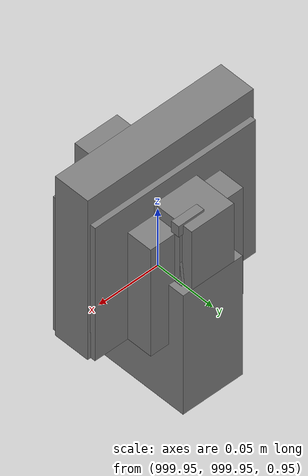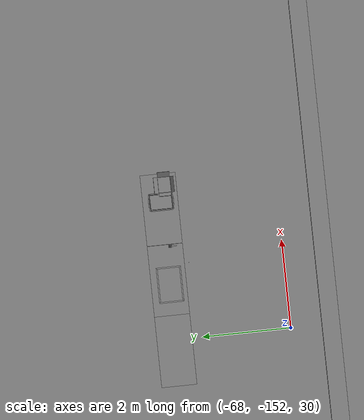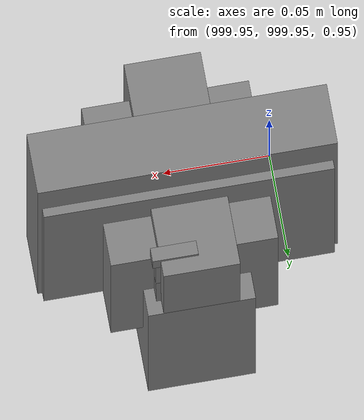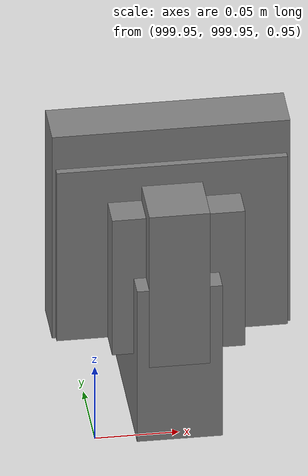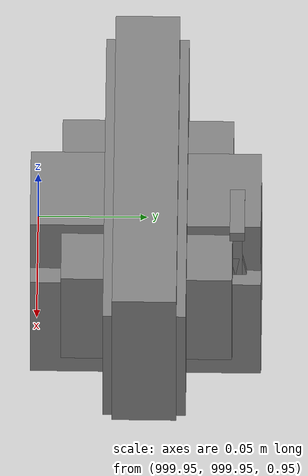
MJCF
<mujoco>
    <option gravity="0.000000000 0.000000000 -9.810000420" timestep="0.0049999999" integrator="implicitfast" density="1.225" viscosity="1.8000001e-05" noslip_iterations="10" iterations="100" sdf_iterations="50">
        <flag multiccd="disable"/>
    </option>
    <size memory="1000M"/>
    <compiler coordinate="local"/>
    <worldbody>
        <light cutoff="30" pos="0 1 1" dir="0 -1 -2"/>
        <light cutoff="30" pos="0 -1 1" dir="0 1 -2"/>
        <body pos="-66.208267212 -149.643096924 31.167007446" euler="156.974868774 24.323186874 -38.511634827" mocap="true" name="spotlight3_SpotLight"/>
        <body pos="1000.000000000 1000.000000000 1.000000000" euler="0.000000000 0.000000000 180.000000000" name="openloong_gripper_2f85_fix_base_usda_battery_01">
            <geom contype="1" conaffinity="1" density="1000" type="box" material="" rgba="0.500000000 0.500000000 0.500000000 1.000000000" solimp="0.899999976 0.949999988 0.001000000" friction="1.000000000 0.005000000 0.000100000" solref="0.020000000 1.000000000" margin="0" condim="3" group="0" pos="-0.011123657 -0.041940309 0.101691343" quat="1.000000000 0.000000000 0.000000000 0.000000000" size="0.010800000 0.003375000 0.004725000" name="openloong_gripper_2f85_fix_base_usda_geom_69EA5FA5_A657_48C7_8F3C_DABBC985087C"/>
            <geom contype="1" conaffinity="1" density="1000" type="box" material="" rgba="0.500000000 0.500000000 0.500000000 1.000000000" solimp="0.899999976 0.949999988 0.001000000" friction="1.000000000 0.005000000 0.000100000" solref="0.020000000 1.000000000" margin="0" condim="3" group="0" pos="-0.010876465 -0.044247437 0.047066893" quat="0.998702705 -0.050920475 0.000000000 0.000000000" size="0.009450001 0.002700000 0.024975000" name="openloong_gripper_2f85_fix_base_usda_geom_21099059_E6AB_41B8_8BF6_9910BB97B914"/>
            <geom contype="1" conaffinity="1" density="1000" type="box" material="" rgba="0.500000000 0.500000000 0.500000000 1.000000000" solimp="0.899999976 0.949999988 0.001000000" friction="1.000000000 0.005000000 0.000100000" solref="0.020000000 1.000000000" margin="0" condim="3" group="0" pos="-0.001235962 -0.000659180 0.047381196" quat="1.000000000 0.000000000 0.000000000 0.000000000" size="0.039420001 0.039150000 0.047250003" name="openloong_gripper_2f85_fix_base_usda_geom_C94A54E1_A119_473A_9057_8DFE8EE4D1FE"/>
            <geom contype="1" conaffinity="1" density="1000" type="box" material="" rgba="0.500000000 0.500000000 0.500000000 1.000000000" solimp="0.899999976 0.949999988 0.001000000" friction="1.000000000 0.005000000 0.000100000" solref="0.020000000 1.000000000" margin="0" condim="3" group="0" pos="-0.010876465 -0.039138794 0.009851727" quat="1.000000000 0.000000000 0.000000000 0.000000000" size="0.009450001 0.010800000 0.013500000" name="openloong_gripper_2f85_fix_base_usda_geom_320F2D9B_2EB9_4C4A_9757_18FC6BF9AE0D"/>
            <geom contype="1" conaffinity="1" density="1000" type="box" material="" rgba="0.500000000 0.500000000 0.500000000 1.000000000" solimp="0.899999976 0.949999988 0.001000000" friction="1.000000000 0.005000000 0.000100000" solref="0.020000000 1.000000000" margin="0" condim="3" group="0" pos="-0.010876465 -0.041528322 0.071508206" quat="1.000000000 0.000000000 0.000000000 0.000000000" size="0.009450001 0.002700000 0.027000001" name="openloong_gripper_2f85_fix_base_usda_geom_4478DBBF_EBF0_4E2B_A338_FC79A6489731"/>
            <freejoint name="openloong_gripper_2f85_fix_base_usda_battery_01_joint"/>
            <site size="0.005000000 0.005000000 0.005000000" rgba="0.500000000 0.500000000 0.500000000 1.000000000" pos="0.000000000 0.000000000 0.000000000" quat="0.999961913 0.008726500 0.000000000 0.000000000" group="0" type="sphere" name="openloong_gripper_2f85_fix_base_usda_battery_01site"/>
        </body>
        <body pos="1000.000000000 1000.000000000 1.000000000" euler="0.000000000 0.000000000 180.000000000" name="openloong_gripper_2f85_fix_base_usda_cpu_fan">
            <geom contype="1" conaffinity="1" density="1000" type="box" material="" rgba="0.500000000 0.500000000 0.500000000 1.000000000" solimp="0.899999976 0.949999988 0.001000000" friction="1.000000000 0.005000000 0.000100000" solref="0.020000000 1.000000000" margin="0" condim="3" group="0" pos="0.000000000 0.000000000 0.070034981" quat="0.000000000 0.000000000 0.000000000 1.000000000" size="0.070700005 0.014699999 0.070700005" name="openloong_gripper_2f85_fix_base_usda_geom_DA771F3B_F8E9_42BD_B99B_F878549BA6C7"/>
            <freejoint name="openloong_gripper_2f85_fix_base_usda_cpu_fan_joint"/>
            <site size="0.005000000 0.005000000 0.005000000" rgba="0.500000000 0.500000000 0.500000000 1.000000000" pos="0.000000000 0.000000000 0.000000000" quat="0.999961913 0.008726535 0.000000000 0.000000000" group="0" type="sphere" name="openloong_gripper_2f85_fix_base_usda_cpu_fancsite"/>
        </body>
        <body pos="1000.000000000 1000.000000000 1.000000000" euler="0.000000000 0.000000000 180.000000000" name="openloong_gripper_2f85_fix_base_usda_wifi_box">
            <geom contype="1" conaffinity="1" density="1000" type="box" material="" rgba="0.500000000 0.500000000 0.500000000 1.000000000" solimp="0.899999976 0.949999988 0.001000000" friction="1.000000000 0.005000000 0.000100000" solref="0.020000000 1.000000000" margin="0" condim="3" group="0" pos="0.000000000 0.000000000 0.058978677" quat="0.000000000 0.000000047 0.000000000 1.000000000" size="0.068499997 0.018999999 0.059000000" name="openloong_gripper_2f85_fix_base_usda_geom_4E7C09B3_4B54_4977_8160_D9C7A5E71C35"/>
            <freejoint name="openloong_gripper_2f85_fix_base_usda_wifi_box_joint"/>
            <site size="0.005000000 0.005000000 0.005000000" rgba="0.500000000 0.500000000 0.500000000 1.000000000" pos="0.000000000 0.000000000 0.000000000" quat="0.999961913 0.008726500 0.000000000 0.000000000" group="0" type="sphere" name="openloong_gripper_2f85_fix_base_usda_wifi_boxsite"/>
        </body>
        <body pos="1000.000000000 1000.000000000 1.000000000" euler="0.000011953 0.000005123 -179.999984741" name="openloong_gripper_2f85_fix_base_usda_intel_box">
            <geom contype="1" conaffinity="1" density="1000" type="box" material="" rgba="0.500000000 0.500000000 0.500000000 1.000000000" solimp="0.899999976 0.949999988 0.001000000" friction="1.000000000 0.005000000 0.000100000" solref="0.020000000 1.000000000" margin="0" condim="3" group="0" pos="0.000000000 -0.000067139 0.000082284" quat="0.707106709 0.000000225 0.000000253 0.707106650" size="0.052800003 0.025300000 0.052800003" name="openloong_gripper_2f85_fix_base_usda_geom_3899827F_22A7_434D_BF2E_DCA0AEF2833E"/>
            <freejoint name="openloong_gripper_2f85_fix_base_usda_intel_box_joint"/>
            <site size="0.005000000 0.005000000 0.005000000" rgba="0.500000000 0.500000000 0.500000000 1.000000000" pos="0.000000000 0.000000000 0.000000000" quat="0.999961913 0.008726500 0.000000000 0.000000000" group="0" type="sphere" name="openloong_gripper_2f85_fix_base_usda_intel_boxsite"/>
        </body>
        <body pos="-65.948188782 -148.954940796 31.170652390" euler="-92.625343323 17.730260849 -139.330932617" mocap="true" name="spotlight5_SpotLight"/>
        <body pos="1000.000000000 999.999938965 1.000000000" euler="0.000000000 0.000000000 180.000000000" name="openloong_gripper_2f85_fix_base_usda_intelcore_i5">
            <geom contype="1" conaffinity="1" density="1000" type="box" material="" rgba="0.500000000 0.500000000 0.500000000 1.000000000" solimp="0.899999976 0.949999988 0.001000000" friction="1.000000000 0.005000000 0.000100000" solref="0.020000000 1.000000000" margin="0" condim="3" group="0" pos="0.000000000 0.000000000 0.051722717" quat="0.707106709 0.000000000 0.000000000 -0.707106769" size="0.052800000 0.018080002 0.052800000" name="openloong_gripper_2f85_fix_base_usda_geom_A88F8ACA_B345_4F5A_AE81_0361A0A9D222"/>
            <freejoint name="openloong_gripper_2f85_fix_base_usda_intelcore_i5_joint"/>
            <site size="0.005000000 0.005000000 0.005000000" rgba="0.500000000 0.500000000 0.500000000 1.000000000" pos="0.000000000 0.000000000 0.000000000" quat="0.999961913 0.008726534 0.000000000 0.000000000" group="0" type="sphere" name="openloong_gripper_2f85_fix_base_usda_intelcore_i5site"/>
        </body>
        <body pos="-65.976928711 -149.682617188 31.165958405" euler="-170.631027222 25.304203033 136.562881470" mocap="true" name="spotlight1_SpotLight"/>
        <body pos="-64.866622925 -149.383972168 30.183746338" euler="89.999984741 89.999946594 0.000000000" name="openloong_gripper_2f85_fix_base_usda_bluebox_01">
            <geom contype="1" conaffinity="1" density="1000" type="box" material="" rgba="0.500000000 0.500000000 0.500000000 1.000000000" solimp="0.899999976 0.949999988 0.001000000" friction="1.000000000 0.005000000 0.000100000" solref="0.020000000 1.000000000" margin="0" condim="3" group="0" pos="0.276580811 0.187225342 0.000068665" quat="0.707106948 0.000077471 0.707106352 0.000077486" size="0.100000001 0.057999998 0.010000000" name="openloong_gripper_2f85_fix_base_usda_geom_30AF8455_7F42_42CC_9811_F53142E480D7"/>
            <geom contype="1" conaffinity="1" density="1000" type="box" material="" rgba="0.500000000 0.500000000 0.500000000 1.000000000" solimp="0.899999976 0.949999988 0.001000000" friction="1.000000000 0.005000000 0.000100000" solref="0.020000000 1.000000000" margin="0" condim="3" group="0" pos="0.000000000 0.002883911 0.000000000" quat="0.999999881 0.000000000 0.000000000 0.000000000" size="0.254000008 0.003000000 0.172000006" name="openloong_gripper_2f85_fix_base_usda_geom_34866CA0_535A_4B17_B377_B6BA673CD7B3"/>
            <geom contype="1" conaffinity="1" density="1000" type="box" material="" rgba="0.500000000 0.500000000 0.500000000 1.000000000" solimp="0.899999976 0.949999988 0.001000000" friction="1.000000000 0.005000000 0.000100000" solref="0.020000000 1.000000000" margin="0" condim="3" group="0" pos="0.000000000 0.124874115 0.173484802" quat="0.999796331 0.020176515 -0.000000015 0.000000030" size="0.259999990 0.119999997 0.007000000" name="openloong_gripper_2f85_fix_base_usda_geom_4BF21AEA_38F1_41A1_A8F4_ACCA332436AD"/>
            <geom contype="1" conaffinity="1" density="1000" type="box" material="" rgba="0.500000000 0.500000000 0.500000000 1.000000000" solimp="0.899999976 0.949999988 0.001000000" friction="1.000000000 0.005000000 0.000100000" solref="0.020000000 1.000000000" margin="0" condim="3" group="0" pos="0.000000000 0.124874115 -0.173469543" quat="0.999796331 -0.020176545 -0.000000015 0.000000000" size="0.259999990 0.119999997 0.007000000" name="openloong_gripper_2f85_fix_base_usda_geom_3B45BA1B_15BA_4A6D_9B75_E5F7B3F675CB"/>
            <geom contype="1" conaffinity="1" density="1000" type="box" material="" rgba="0.500000000 0.500000000 0.500000000 1.000000000" solimp="0.899999976 0.949999988 0.001000000" friction="1.000000000 0.005000000 0.000100000" solref="0.020000000 1.000000000" margin="0" condim="3" group="0" pos="0.000000000 0.214008331 0.188980103" quat="0.999912977 0.013176724 0.000000015 0.000000000" size="0.259999990 0.029999999 0.012500000" name="openloong_gripper_2f85_fix_base_usda_geom_EBCA9720_B522_444C_ABE1_2D8B0AE2CF4A"/>
            <geom contype="1" conaffinity="1" density="1000" type="box" material="" rgba="0.500000000 0.500000000 0.500000000 1.000000000" solimp="0.899999976 0.949999988 0.001000000" friction="1.000000000 0.005000000 0.000100000" solref="0.020000000 1.000000000" margin="0" condim="3" group="0" pos="-0.258361816 0.125289917 0.001876831" quat="0.702796936 -0.020792112 0.710783124 0.020769298" size="0.189999998 0.119999997 0.009000000" name="openloong_gripper_2f85_fix_base_usda_geom_A3080891_C89B_4563_95A1_C71AD9A3DF2E"/>
            <geom contype="1" conaffinity="1" density="1000" type="box" material="" rgba="0.500000000 0.500000000 0.500000000 1.000000000" solimp="0.899999976 0.949999988 0.001000000" friction="1.000000000 0.005000000 0.000100000" solref="0.020000000 1.000000000" margin="0" condim="3" group="0" pos="0.000000000 0.214008331 -0.188980103" quat="0.999912977 -0.013176769 0.000000030 0.000000015" size="0.259999990 0.029999999 0.012500000" name="openloong_gripper_2f85_fix_base_usda_geom_6E32BD6F_E718_410A_AF78_AB9E78A6DD85"/>
            <geom contype="1" conaffinity="1" density="1000" type="box" material="" rgba="0.500000000 0.500000000 0.500000000 1.000000000" solimp="0.899999976 0.949999988 0.001000000" friction="1.000000000 0.005000000 0.000100000" solref="0.020000000 1.000000000" margin="0" condim="3" group="0" pos="-0.276611328 0.187225342 0.000068665" quat="0.707106650 0.000077441 0.707106709 0.000077456" size="0.100000001 0.057999998 0.010000000" name="openloong_gripper_2f85_fix_base_usda_geom_11578F44_58BE_427C_AD59_FAF1A1C64F04"/>
            <geom contype="1" conaffinity="1" density="1000" type="box" material="" rgba="0.500000000 0.500000000 0.500000000 1.000000000" solimp="0.899999976 0.949999988 0.001000000" friction="1.000000000 0.005000000 0.000100000" solref="0.020000000 1.000000000" margin="0" condim="3" group="0" pos="0.258331299 0.125289917 0.001876831" quat="0.702851415 0.018856421 0.710823774 -0.019329369" size="0.189999998 0.119999997 0.009000000" name="openloong_gripper_2f85_fix_base_usda_geom_7B27B4D6_EC85_45BB_80D1_A8B3187C84AE"/>
            <freejoint name="openloong_gripper_2f85_fix_base_usda_bluebox_01_joint"/>
            <site size="0.005000000 0.005000000 0.005000000" rgba="0.500000000 0.500000000 0.500000000 1.000000000" pos="0.000000000 0.000000000 0.000000000" quat="0.999961913 0.008726534 0.000000000 0.000000000" group="0" type="sphere" name="openloong_gripper_2f85_fix_base_usda_bluebox_01site"/>
        </body>
        <body pos="-64.496299744 -149.491867065 30.235729218" euler="0.000000000 0.000000000 89.999946594" name="openloong_gripper_2f85_fix_base_usda_cardboardbox_01">
            <geom contype="1" conaffinity="1" density="1000" type="box" material="" rgba="0.500000000 0.500000000 0.500000000 1.000000000" solimp="0.899999976 0.949999988 0.001000000" friction="1.000000000 0.005000000 0.000100000" solref="0.020000000 1.000000000" margin="0" condim="3" group="0" pos="-0.003166199 -0.004086494 0.005052090" quat="1.000000000 0.000000000 0.000000000 0.000000000" size="0.142499998 0.177500010 0.005000000" name="openloong_gripper_2f85_fix_base_usda_geom_5E57BEA9_DC4E_4D2E_8898_0969181D2EE2"/>
            <geom contype="1" conaffinity="1" density="1000" type="box" material="" rgba="0.500000000 0.500000000 0.500000000 1.000000000" solimp="0.899999976 0.949999988 0.001000000" friction="1.000000000 0.005000000 0.000100000" solref="0.020000000 1.000000000" margin="0" condim="3" group="0" pos="-0.003166199 0.170316696 0.150570869" quat="1.000000000 0.000000000 0.000000000 0.000000000" size="0.142499998 0.005000000 0.149999991" name="openloong_gripper_2f85_fix_base_usda_geom_A1264B22_3025_45D6_A7F7_6148A0E47E0F"/>
            <geom contype="1" conaffinity="1" density="1000" type="box" material="" rgba="0.500000000 0.500000000 0.500000000 1.000000000" solimp="0.899999976 0.949999988 0.001000000" friction="1.000000000 0.005000000 0.000100000" solref="0.020000000 1.000000000" margin="0" condim="3" group="0" pos="-0.147399902 -0.005307198 0.150570869" quat="1.000000000 0.000000000 0.000000000 0.000000000" size="0.005000000 0.177500010 0.149999991" name="openloong_gripper_2f85_fix_base_usda_geom_077D7179_7927_4046_98DF_E596D25D7D99"/>
            <geom contype="1" conaffinity="1" density="1000" type="box" material="" rgba="0.500000000 0.500000000 0.500000000 1.000000000" solimp="0.899999976 0.949999988 0.001000000" friction="1.000000000 0.005000000 0.000100000" solref="0.020000000 1.000000000" margin="0" condim="3" group="0" pos="0.140275955 -0.005307198 0.150570869" quat="1.000000000 0.000000000 0.000000000 0.000000000" size="0.005000000 0.177500010 0.149999991" name="openloong_gripper_2f85_fix_base_usda_geom_6952CA05_D60D_4399_9797_AA312345E904"/>
            <geom contype="1" conaffinity="1" density="1000" type="box" material="" rgba="0.500000000 0.500000000 0.500000000 1.000000000" solimp="0.899999976 0.949999988 0.001000000" friction="1.000000000 0.005000000 0.000100000" solref="0.020000000 1.000000000" margin="0" condim="3" group="0" pos="-0.003166199 -0.181550980 0.150570869" quat="1.000000000 0.000000000 0.000000000 0.000000000" size="0.142499998 0.005000000 0.149999991" name="openloong_gripper_2f85_fix_base_usda_geom_4D5F0121_BABA_4039_9F4D_9B13C692461C"/>
            <freejoint name="openloong_gripper_2f85_fix_base_usda_cardboardbox_01_joint"/>
            <site size="0.005000000 0.005000000 0.005000000" rgba="0.500000000 0.500000000 0.500000000 1.000000000" pos="0.000000000 0.000000000 0.000000000" quat="0.999961913 0.008726535 0.000000000 0.000000000" group="0" type="sphere" name="openloong_gripper_2f85_fix_base_usda_site_4F7AE0C2_F9EB_46FD_B12F_4DF4EE0A68C6"/>
            <body pos="0.139160156 -0.004048347 0.301930904" euler="-179.999954224 49.383502960 179.999954224" name="openloong_gripper_2f85_fix_base_usda_A1_006">
                <geom contype="1" conaffinity="1" density="1000" type="box" material="" rgba="0.500000000 0.500000000 0.500000000 1.000000000" solimp="0.899999976 0.949999988 0.001000000" friction="1.000000000 0.005000000 0.000100000" solref="0.020000000 1.000000000" margin="0" condim="3" group="0" pos="-0.071587563 0.000009537 0.001745224" quat="0.999999881 0.000000000 0.000000000 0.000000000" size="0.071249999 0.179999992 0.002500000" name="openloong_gripper_2f85_fix_base_usda_geom_0E802031_3A8C_40EB_8110_05E7FD0747CD"/>
                <joint armature="0" stiffness="0.07" damping="0.0099999998" axis="0.000000 1.000000 0.000000" type="hinge" name="openloong_gripper_2f85_fix_base_usda_A1_006"/>
            </body>
            <body pos="-0.145902634 -0.004086494 0.301938057" euler="-180.000000000 -60.000011444 -180.000000000" name="openloong_gripper_2f85_fix_base_usda_A2_006">
                <geom contype="1" conaffinity="1" density="1000" type="box" material="" rgba="0.500000000 0.500000000 0.500000000 1.000000000" solimp="0.899999976 0.949999988 0.001000000" friction="1.000000000 0.005000000 0.000100000" solref="0.020000000 1.000000000" margin="0" condim="3" group="0" pos="0.071268082 0.000009537 0.002717972" quat="0.000002921 0.000000000 -0.000000030 0.999999881" size="0.071249999 0.179999992 0.002500000" name="openloong_gripper_2f85_fix_base_usda_geom_C42A5395_F195_46A4_9C8E_DFC53D325640"/>
                <joint armature="0" stiffness="0.07" damping="0.0099999998" axis="0.000000 1.000000 0.000000" type="hinge" name="openloong_gripper_2f85_fix_base_usda_A2_006"/>
            </body>
            <body pos="-0.003385544 0.175991058 0.301930904" euler="-125.858116150 -0.000004561 0.000002331" name="openloong_gripper_2f85_fix_base_usda_B2_006">
                <geom contype="1" conaffinity="1" density="1000" type="box" material="" rgba="0.500000000 0.500000000 0.500000000 1.000000000" solimp="0.899999976 0.949999988 0.001000000" friction="1.000000000 0.005000000 0.000100000" solref="0.020000000 1.000000000" margin="0" condim="3" group="0" pos="0.000009537 -0.070939064 -0.002470016" quat="0.999614120 0.027776197 -0.000000015 0.000000030" size="0.137500003 0.064999998 0.005000000" name="openloong_gripper_2f85_fix_base_usda_geom_E0BFC823_FD86_4BAB_9E14_87B674CB33F0"/>
                <joint armature="0" stiffness="0.07" damping="0.0099999998" axis="1.000000 0.000000 0.000000" type="hinge" name="openloong_gripper_2f85_fix_base_usda_B2_006"/>
            </body>
            <body pos="-0.003385544 -0.184140205 0.301938057" euler="147.805557251 0.000000000 0.000000000" name="openloong_gripper_2f85_fix_base_usda_B1_006">
                <geom contype="1" conaffinity="1" density="1000" type="box" material="" rgba="0.500000000 0.500000000 0.500000000 1.000000000" solimp="0.899999976 0.949999988 0.001000000" friction="1.000000000 0.005000000 0.000100000" solref="0.020000000 1.000000000" margin="0" condim="3" group="0" pos="-0.000028610 0.070202351 -0.002703667" quat="0.999614179 -0.027776167 0.000000000 0.000000000" size="0.137500003 0.064999998 0.005000000" name="openloong_gripper_2f85_fix_base_usda_geom_B2A74602_B179_4DF7_91FA_4CC6FC8870A8"/>
                <joint armature="0" stiffness="0.07" damping="0.0099999998" axis="1.000000 0.000000 0.000000" type="hinge" name="openloong_gripper_2f85_fix_base_usda_B1_006"/>
            </body>
        </body>
        <body pos="-65.882858276 -149.481979370 30.229999542" euler="-64.487716675 0.000000000 0.000000000" name="openloong_gripper_2f85_fix_base_usda_Barcode">
            <geom contype="1" conaffinity="1" density="1000" type="box" material="" rgba="0.500000000 0.500000000 0.500000000 1.000000000" solimp="0.899999976 0.949999988 0.001000000" friction="1.000000000 0.005000000 0.000100000" solref="0.020000000 1.000000000" margin="0" condim="3" group="0" pos="0.000000000 0.013038635 0.001419067" quat="0.000000000 0.000000000 0.000000000 1.000000119" size="0.034000002 0.010000000 0.017999999" name="openloong_gripper_2f85_fix_base_usda_geom_ED09B279_51C1_40D9_AF5B_80D725BF76B5"/>
            <geom contype="1" conaffinity="1" density="1000" type="box" material="" rgba="0.500000000 0.500000000 0.500000000 1.000000000" solimp="0.899999976 0.949999988 0.001000000" friction="1.000000000 0.005000000 0.000100000" solref="0.020000000 1.000000000" margin="0" condim="3" group="0" pos="0.000000000 -0.035301208 -0.007095337" quat="0.000000000 0.000000000 -0.043619365 0.999048233" size="0.028999999 0.010000000 0.020000000" name="openloong_gripper_2f85_fix_base_usda_geom_711F4B26_8E47_4ED8_886A_A8740D79F015"/>
            <geom contype="1" conaffinity="1" density="1000" type="box" material="" rgba="0.500000000 0.500000000 0.500000000 1.000000000" solimp="0.899999976 0.949999988 0.001000000" friction="1.000000000 0.005000000 0.000100000" solref="0.020000000 1.000000000" margin="0" condim="3" group="0" pos="0.000000000 -0.043411255 -0.011749268" quat="0.922262907 0.386563420 0.000000000 0.000000000" size="0.026000001 0.010000000 0.020000000" name="openloong_gripper_2f85_fix_base_usda_geom_F04C1C96_6F7C_47C4_A297_A4E56D9F7699"/>
            <geom contype="1" conaffinity="1" density="1000" type="box" material="" rgba="0.500000000 0.500000000 0.500000000 1.000000000" solimp="0.899999976 0.949999988 0.001000000" friction="1.000000000 0.005000000 0.000100000" solref="0.020000000 1.000000000" margin="0" condim="3" group="0" pos="0.000000000 -0.016967773 -0.031860352" quat="0.000000000 0.000000000 0.000000000 1.000000119" size="0.008000000 0.010000000 0.013000000" name="openloong_gripper_2f85_fix_base_usda_geom_EBD874C6_4A45_4D0B_80F8_512C3EDCC556"/>
            <geom contype="1" conaffinity="1" density="1000" type="box" material="" rgba="0.500000000 0.500000000 0.500000000 1.000000000" solimp="0.899999976 0.949999988 0.001000000" friction="1.000000000 0.005000000 0.000100000" solref="0.020000000 1.000000000" margin="0" condim="3" group="0" pos="0.000000000 -0.001869202 0.000312805" quat="0.953716993 0.300705761 0.000000000 0.000000000" size="0.032000002 0.010000000 0.018999999" name="openloong_gripper_2f85_fix_base_usda_geom_FF70D11D_9A1F_44D3_A269_C5C910623EA3"/>
            <geom contype="1" conaffinity="1" density="1000" type="box" material="" rgba="0.500000000 0.500000000 0.500000000 1.000000000" solimp="0.899999976 0.949999988 0.001000000" friction="1.000000000 0.005000000 0.000100000" solref="0.020000000 1.000000000" margin="0" condim="3" group="0" pos="0.000000000 -0.019531250 -0.003173828" quat="0.953716993 0.300705761 0.000000000 0.000000000" size="0.030999999 0.010000000 0.020000000" name="openloong_gripper_2f85_fix_base_usda_geom_F4D6A651_FF04_446A_A156_EF0EB9B4A69E"/>
            <geom contype="1" conaffinity="1" density="1000" type="box" material="" rgba="0.500000000 0.500000000 0.500000000 1.000000000" solimp="0.899999976 0.949999988 0.001000000" friction="1.000000000 0.005000000 0.000100000" solref="0.020000000 1.000000000" margin="0" condim="3" group="0" pos="0.000000000 -0.035301208 -0.007095337" quat="0.953716993 0.300705761 0.000000000 0.000000000" size="0.028999999 0.010000000 0.020000000" name="openloong_gripper_2f85_fix_base_usda_geom_16E89405_DD22_4772_A645_47496E0914CD"/>
            <geom contype="1" conaffinity="1" density="1000" type="box" material="" rgba="0.500000000 0.500000000 0.500000000 1.000000000" solimp="0.899999976 0.949999988 0.001000000" friction="1.000000000 0.005000000 0.000100000" solref="0.020000000 1.000000000" margin="0" condim="3" group="0" pos="0.000000000 -0.042617798 -0.071121216" quat="0.000000000 0.000000000 0.000000000 1.000000119" size="0.013000000 0.021000000 0.059999999" name="openloong_gripper_2f85_fix_base_usda_geom_EA7763BB_C85A_4555_822B_635479EBDFC9"/>
            <freejoint name="openloong_gripper_2f85_fix_base_usda_Barcode_joint"/>
            <site size="0.005000000 0.005000000 0.005000000" rgba="0.500000000 0.500000000 0.500000000 1.000000000" pos="0.000000000 0.000000000 0.000000000" quat="1.000000000 0.000000000 0.000000000 0.000000000" group="0" type="sphere" name="openloong_gripper_2f85_fix_base_usda_Barcode_site"/>
        </body>
        <body pos="-66.745018005 -149.392349243 30.184000015" euler="0.000000000 0.000000000 89.999946594" name="[22330868049429]_Basket_01">
            <geom contype="1" conaffinity="1" density="1000" type="box" material="" rgba="0.500000000 0.500000000 0.500000000 1.000000000" solimp="0.899999976 0.949999988 0.001000000" friction="1.000000000 0.005000000 0.000100000" solref="0.020000000 1.000000000" margin="0" condim="3" group="0" pos="-0.052425385 0.389207840 0.089787483" quat="0.707107008 0.000000000 0.000000000 0.707106411" size="0.014249999 0.014249999 0.059999999" name="[22330868049429]_geom_3CE19E7E_0CF7_4369_8C29_3E174627256A"/>
            <geom contype="1" conaffinity="1" density="1000" type="box" material="" rgba="0.500000000 0.500000000 0.500000000 1.000000000" solimp="0.899999976 0.949999988 0.001000000" friction="1.000000000 0.005000000 0.000100000" solref="0.020000000 1.000000000" margin="0" condim="3" group="0" pos="0.264015198 -0.133043289 0.089787483" quat="0.707107008 0.000000000 0.000000000 0.707106411" size="0.014249999 0.014249999 0.059999999" name="[22330868049429]_geom_3A859A2A_D303_408D_BBEB_5EA43EF08B2B"/>
            <geom contype="1" conaffinity="1" density="1000" type="box" material="" rgba="0.500000000 0.500000000 0.500000000 1.000000000" solimp="0.899999976 0.949999988 0.001000000" friction="1.000000000 0.005000000 0.000100000" solref="0.020000000 1.000000000" margin="0" condim="3" group="0" pos="-0.264015198 -0.265548706 0.089793205" quat="0.707107008 0.000000000 0.000000000 0.707106411" size="0.014249999 0.014249999 0.059999999" name="[22330868049429]_geom_F8CB1305_AA16_4A12_B0AC_B405502B623D"/>
            <geom contype="1" conaffinity="1" density="1000" type="box" material="" rgba="0.500000000 0.500000000 0.500000000 1.000000000" solimp="0.899999976 0.949999988 0.001000000" friction="1.000000000 0.005000000 0.000100000" solref="0.020000000 1.000000000" margin="0" condim="3" group="0" pos="-0.160263062 -0.389322281 0.089793205" quat="0.707107008 0.000000000 0.000000000 0.707106411" size="0.014249999 0.014249999 0.059999999" name="[22330868049429]_geom_510C53DC_4DCA_4073_B229_994D3DDDA5ED"/>
            <geom contype="1" conaffinity="1" density="1000" type="box" material="" rgba="0.500000000 0.500000000 0.500000000 1.000000000" solimp="0.899999976 0.949999988 0.001000000" friction="1.000000000 0.005000000 0.000100000" solref="0.020000000 1.000000000" margin="0" condim="3" group="0" pos="0.162265778 -0.389322281 0.089787483" quat="0.707107008 0.000000000 0.000000000 0.707106411" size="0.014249999 0.014249999 0.059999999" name="[22330868049429]_geom_CA3C5DE5_CF11_446F_8559_F0EB56BBA12C"/>
            <geom contype="1" conaffinity="1" density="1000" type="box" material="" rgba="0.500000000 0.500000000 0.500000000 1.000000000" solimp="0.899999976 0.949999988 0.001000000" friction="1.000000000 0.005000000 0.000100000" solref="0.020000000 1.000000000" margin="0" condim="3" group="0" pos="0.264015198 0.389207840 0.089787483" quat="0.707107008 0.000000000 0.000000000 0.707106411" size="0.014249999 0.014249999 0.059999999" name="[22330868049429]_geom_23DF73B2_A6A3_4E3F_96D0_7D8864C0AB00"/>
            <geom contype="1" conaffinity="1" density="1000" type="box" material="" rgba="0.500000000 0.500000000 0.500000000 1.000000000" solimp="0.899999976 0.949999988 0.001000000" friction="1.000000000 0.005000000 0.000100000" solref="0.020000000 1.000000000" margin="0" condim="3" group="0" pos="-0.264015198 -0.133043289 0.089793205" quat="0.707107008 0.000000000 0.000000000 0.707106411" size="0.014249999 0.014249999 0.059999999" name="[22330868049429]_geom_166BD87C_A625_4597_8F73_60C09AEFC636"/>
            <geom contype="1" conaffinity="1" density="1000" type="box" material="" rgba="0.500000000 0.500000000 0.500000000 1.000000000" solimp="0.899999976 0.949999988 0.001000000" friction="1.000000000 0.005000000 0.000100000" solref="0.020000000 1.000000000" margin="0" condim="3" group="0" pos="-0.264026642 0.269256592 0.089793205" quat="0.707107008 0.000000000 0.000000000 0.707106411" size="0.014249999 0.014249999 0.059999999" name="[22330868049429]_geom_F60045D5_51EF_4CC5_918E_937F4B210B01"/>
            <geom contype="1" conaffinity="1" density="1000" type="box" material="" rgba="0.500000000 0.500000000 0.500000000 1.000000000" solimp="0.899999976 0.949999988 0.001000000" friction="1.000000000 0.005000000 0.000100000" solref="0.020000000 1.000000000" margin="0" condim="3" group="0" pos="0.054462433 0.389207840 0.089787483" quat="0.707107008 0.000000000 0.000000000 0.707106411" size="0.014249999 0.014249999 0.059999999" name="[22330868049429]_geom_68350A1D_1325_4926_9F80_4BBE14403976"/>
            <geom contype="1" conaffinity="1" density="1000" type="box" material="" rgba="0.500000000 0.500000000 0.500000000 1.000000000" solimp="0.899999976 0.949999988 0.001000000" friction="1.000000000 0.005000000 0.000100000" solref="0.020000000 1.000000000" margin="0" condim="3" group="0" pos="0.054462433 -0.389322281 0.089787483" quat="0.707107008 0.000000000 0.000000000 0.707106411" size="0.014249999 0.014249999 0.059999999" name="[22330868049429]_geom_57130B7C_8FFA_4A28_A16F_3D2D119002C7"/>
            <geom contype="1" conaffinity="1" density="1000" type="box" material="" rgba="0.500000000 0.500000000 0.500000000 1.000000000" solimp="0.899999976 0.949999988 0.001000000" friction="1.000000000 0.005000000 0.000100000" solref="0.020000000 1.000000000" margin="0" condim="3" group="0" pos="0.264015198 0.269256592 0.089793205" quat="0.707107008 0.000000000 0.000000000 0.707106411" size="0.014249999 0.014249999 0.059999999" name="[22330868049429]_geom_B0EF5E31_C824_4378_A94D_0174F370A949"/>
            <geom contype="1" conaffinity="1" density="1000" type="box" material="" rgba="0.500000000 0.500000000 0.500000000 1.000000000" solimp="0.899999976 0.949999988 0.001000000" friction="1.000000000 0.005000000 0.000100000" solref="0.020000000 1.000000000" margin="0" condim="3" group="0" pos="0.264015198 -0.389322281 0.089787483" quat="0.707107008 0.000000000 0.000000000 0.707106411" size="0.014249999 0.014249999 0.059999999" name="[22330868049429]_geom_725353E0_CA8F_4DBF_9F63_5CCB84E479EE"/>
            <geom contype="1" conaffinity="1" density="1000" type="box" material="" rgba="0.500000000 0.500000000 0.500000000 1.000000000" solimp="0.899999976 0.949999988 0.001000000" friction="1.000000000 0.005000000 0.000100000" solref="0.020000000 1.000000000" margin="0" condim="3" group="0" pos="0.000000000 0.000000000 0.015998840" quat="0.707107008 0.000000000 0.000000000 0.707106411" size="0.403499991 0.279000014 0.015750000" name="[22330868049429]_geom_5EF8FE07_714E_4743_88E6_0BEF586E383C"/>
            <geom contype="1" conaffinity="1" density="1000" type="box" material="" rgba="0.500000000 0.500000000 0.500000000 1.000000000" solimp="0.899999976 0.949999988 0.001000000" friction="1.000000000 0.005000000 0.000100000" solref="0.020000000 1.000000000" margin="0" condim="3" group="0" pos="0.000000000 -0.389476776 0.163619041" quat="0.707107008 0.000000000 0.000000000 0.707106411" size="0.015000000 0.277500004 0.015750000" name="[22330868049429]_geom_B1F649FC_044F_4B0B_8769_00FB8080FF37"/>
            <geom contype="1" conaffinity="1" density="1000" type="box" material="" rgba="0.500000000 0.500000000 0.500000000 1.000000000" solimp="0.899999976 0.949999988 0.001000000" friction="1.000000000 0.005000000 0.000100000" solref="0.020000000 1.000000000" margin="0" condim="3" group="0" pos="0.162265778 0.389207840 0.089787483" quat="0.707107008 0.000000000 0.000000000 0.707106411" size="0.014249999 0.014249999 0.059999999" name="[22330868049429]_geom_87E74172_4A1D_4BDB_AE86_964D47783904"/>
            <geom contype="1" conaffinity="1" density="1000" type="box" material="" rgba="0.500000000 0.500000000 0.500000000 1.000000000" solimp="0.899999976 0.949999988 0.001000000" friction="1.000000000 0.005000000 0.000100000" solref="0.020000000 1.000000000" margin="0" condim="3" group="0" pos="0.000000000 0.389471054 0.163619041" quat="0.707107008 0.000000000 0.000000000 0.707106411" size="0.015000000 0.277500004 0.015750000" name="[22330868049429]_geom_42510960_9226_474E_A507_7EFB1341321D"/>
            <geom contype="1" conaffinity="1" density="1000" type="box" material="" rgba="0.500000000 0.500000000 0.500000000 1.000000000" solimp="0.899999976 0.949999988 0.001000000" friction="1.000000000 0.005000000 0.000100000" solref="0.020000000 1.000000000" margin="0" condim="3" group="0" pos="-0.263511658 0.000000000 0.163619041" quat="0.707107008 0.000000000 0.000000000 0.707106411" size="0.403499991 0.015000000 0.015750000" name="[22330868049429]_geom_9B0A69A4_8063_491C_A3A9_A5D13AAD0A29"/>
            <geom contype="1" conaffinity="1" density="1000" type="box" material="" rgba="0.500000000 0.500000000 0.500000000 1.000000000" solimp="0.899999976 0.949999988 0.001000000" friction="1.000000000 0.005000000 0.000100000" solref="0.020000000 1.000000000" margin="0" condim="3" group="0" pos="-0.264015198 0.141334534 0.089793205" quat="0.707107008 0.000000000 0.000000000 0.707106411" size="0.014249999 0.014249999 0.059999999" name="[22330868049429]_geom_F3CA5E97_5159_4E93_AAFE_F4ADE5A62D9E"/>
            <geom contype="1" conaffinity="1" density="1000" type="box" material="" rgba="0.500000000 0.500000000 0.500000000 1.000000000" solimp="0.899999976 0.949999988 0.001000000" friction="1.000000000 0.005000000 0.000100000" solref="0.020000000 1.000000000" margin="0" condim="3" group="0" pos="0.264015198 -0.265548706 0.089787483" quat="0.707107008 0.000000000 0.000000000 0.707106411" size="0.014249999 0.014249999 0.059999999" name="[22330868049429]_geom_2D5AD79E_22DE_4276_AE2B_88B95A1AFC3E"/>
            <geom contype="1" conaffinity="1" density="1000" type="box" material="" rgba="0.500000000 0.500000000 0.500000000 1.000000000" solimp="0.899999976 0.949999988 0.001000000" friction="1.000000000 0.005000000 0.000100000" solref="0.020000000 1.000000000" margin="0" condim="3" group="0" pos="-0.160263062 0.389207840 0.089787483" quat="0.707107008 0.000000000 0.000000000 0.707106411" size="0.014249999 0.014249999 0.059999999" name="[22330868049429]_geom_7540F47F_509F_4A80_A012_215B8949591A"/>
            <geom contype="1" conaffinity="1" density="1000" type="box" material="" rgba="0.500000000 0.500000000 0.500000000 1.000000000" solimp="0.899999976 0.949999988 0.001000000" friction="1.000000000 0.005000000 0.000100000" solref="0.020000000 1.000000000" margin="0" condim="3" group="0" pos="-0.052425385 -0.389322281 0.089787483" quat="0.707107008 0.000000000 0.000000000 0.707106411" size="0.014249999 0.014249999 0.059999999" name="[22330868049429]_geom_F516D204_0AB3_47F1_895F_19C28D9364E6"/>
            <geom contype="1" conaffinity="1" density="1000" type="box" material="" rgba="0.500000000 0.500000000 0.500000000 1.000000000" solimp="0.899999976 0.949999988 0.001000000" friction="1.000000000 0.005000000 0.000100000" solref="0.020000000 1.000000000" margin="0" condim="3" group="0" pos="-0.264026642 -0.389322281 0.089793205" quat="0.707107008 0.000000000 0.000000000 0.707106411" size="0.014249999 0.014249999 0.059999999" name="[22330868049429]_geom_69CCC3D5_0786_46E3_B35F_0DB2560E6A73"/>
            <geom contype="1" conaffinity="1" density="1000" type="box" material="" rgba="0.500000000 0.500000000 0.500000000 1.000000000" solimp="0.899999976 0.949999988 0.001000000" friction="1.000000000 0.005000000 0.000100000" solref="0.020000000 1.000000000" margin="0" condim="3" group="0" pos="0.264015198 0.141334534 0.089787483" quat="0.707107008 0.000000000 0.000000000 0.707106411" size="0.014249999 0.014249999 0.059999999" name="[22330868049429]_geom_3DC7D4DC_CA98_4124_B880_30F92EF36485"/>
            <geom contype="1" conaffinity="1" density="1000" type="box" material="" rgba="0.500000000 0.500000000 0.500000000 1.000000000" solimp="0.899999976 0.949999988 0.001000000" friction="1.000000000 0.005000000 0.000100000" solref="0.020000000 1.000000000" margin="0" condim="3" group="0" pos="-0.264015198 0.389207840 0.089793205" quat="0.707107008 0.000000000 0.000000000 0.707106411" size="0.014249999 0.014249999 0.059999999" name="[22330868049429]_geom_B15C90BC_360C_4A33_BE7D_8FB4864C5EBD"/>
            <geom contype="1" conaffinity="1" density="1000" type="box" material="" rgba="0.500000000 0.500000000 0.500000000 1.000000000" solimp="0.899999976 0.949999988 0.001000000" friction="1.000000000 0.005000000 0.000100000" solref="0.020000000 1.000000000" margin="0" condim="3" group="0" pos="0.264015198 0.004480362 0.089787483" quat="0.707107008 0.000000000 0.000000000 0.707106411" size="0.014249999 0.014249999 0.059999999" name="[22330868049429]_geom_FD9CB653_FF46_45B2_B479_3D6D64F134C6"/>
            <geom contype="1" conaffinity="1" density="1000" type="box" material="" rgba="0.500000000 0.500000000 0.500000000 1.000000000" solimp="0.899999976 0.949999988 0.001000000" friction="1.000000000 0.005000000 0.000100000" solref="0.020000000 1.000000000" margin="0" condim="3" group="0" pos="0.263694763 -0.000011444 0.163619041" quat="0.707107008 0.000000000 0.000000000 0.707106411" size="0.403499991 0.015000000 0.015750000" name="[22330868049429]_geom_EF794062_B9E3_4980_B116_4E82843C9B95"/>
            <geom contype="1" conaffinity="1" density="1000" type="box" material="" rgba="0.500000000 0.500000000 0.500000000 1.000000000" solimp="0.899999976 0.949999988 0.001000000" friction="1.000000000 0.005000000 0.000100000" solref="0.020000000 1.000000000" margin="0" condim="3" group="0" pos="-0.264015198 0.004480362 0.089793205" quat="0.707107008 0.000000000 0.000000000 0.707106411" size="0.014249999 0.014249999 0.059999999" name="[22330868049429]_geom_D7E208A0_509B_458D_BEF5_4F46FBD7595B"/>
            <freejoint name="[22330868049429]_joint_6FFF7D8B_2A0C_418C_85CE_CFB15AB5BA8B"/>
        </body>
        <body pos="0.000000000 0.000000000 0.000000000" euler="0.000000000 0.000000000 0.000000000" name="Static Objects_Static Objects">
            <geom contype="1" conaffinity="1" density="1000" type="box" material="" rgba="0.500000000 0.500000000 0.500000000 1.000000000" solimp="0.899999976 0.949999988 0.001000000" friction="1.000000000 0.005000000 0.000100000" solref="0.020000000 1.000000000" margin="0" condim="3" group="0" pos="-67.544113159 -149.365814209 29.727830887" quat="0.500000417 0.499999970 0.499999553 0.499999970" size="0.381000012 0.319999993 0.041000001" name="Static Objects_geom_BA9DC545_B1D3_4BE1_8F93_FEBBF646710E"/>
            <geom contype="1" conaffinity="1" density="1000" type="box" material="" rgba="0.500000000 0.500000000 0.500000000 1.000000000" solimp="0.899999976 0.949999988 0.001000000" friction="1.000000000 0.005000000 0.000100000" solref="0.020000000 1.000000000" margin="0" condim="3" group="0" pos="-68.239501953 -149.365814209 30.086868286" quat="0.500000417 0.499999970 0.499999553 0.499999970" size="0.370999992 0.039500002 0.745000005" name="Static Objects_geom_CF4203F8_F542_4226_BBA8_3E6C552D1D64"/>
            <geom contype="1" conaffinity="1" density="1000" type="box" material="" rgba="0.500000000 0.500000000 0.500000000 1.000000000" solimp="0.899999976 0.949999988 0.001000000" friction="1.000000000 0.005000000 0.000100000" solref="0.020000000 1.000000000" margin="0" condim="3" group="0" pos="-68.239501953 -149.365814209 30.147235870" quat="0.500000417 0.499999970 0.499999553 0.499999970" size="0.400000006 0.022000000 0.800000012" name="Static Objects_geom_02A2C76A_0F14_464A_ACB4_867E1B07A116"/>
            <geom contype="1" conaffinity="1" density="1000" type="box" material="" rgba="0.500000000 0.500000000 0.500000000 1.000000000" solimp="0.899999976 0.949999988 0.001000000" friction="1.000000000 0.005000000 0.000100000" solref="0.020000000 1.000000000" margin="0" condim="3" group="0" pos="-68.934890747 -149.365814209 29.727830887" quat="0.500000417 0.499999970 0.499999553 0.499999970" size="0.381000012 0.319999993 0.041000001" name="Static Objects_geom_3D3BB336_6CC0_4AC1_BCB0_752CEEA0FE29"/>
            <geom contype="1" conaffinity="1" density="1000" type="box" material="" rgba="0.500000000 0.500000000 0.500000000 1.000000000" solimp="0.899999976 0.949999988 0.001000000" friction="1.000000000 0.005000000 0.000100000" solref="0.020000000 1.000000000" margin="0" condim="3" group="0" pos="-68.239501953 -149.365814209 29.561563492" quat="0.500000417 0.499999970 0.499999553 0.499999970" size="0.020000000 0.022000000 0.660000026" name="Static Objects_geom_DF3E7ACE_17F5_418C_A37F_1F48152A5047"/>
            <geom contype="1" conaffinity="1" density="1000" type="box" material="" rgba="0.500000000 0.500000000 0.500000000 1.000000000" solimp="0.899999976 0.949999988 0.001000000" friction="1.000000000 0.005000000 0.000100000" solref="0.020000000 1.000000000" margin="0" condim="3" group="0" pos="-65.945671082 -149.365814209 29.727830887" quat="0.500000417 0.499999970 0.499999553 0.499999970" size="0.381000012 0.319999993 0.041000001" name="Static Objects_geom_1769CB19_7BA9_455E_AB25_B8689FC0ECB9"/>
            <geom contype="1" conaffinity="1" density="1000" type="box" material="" rgba="0.500000000 0.500000000 0.500000000 1.000000000" solimp="0.899999976 0.949999988 0.001000000" friction="1.000000000 0.005000000 0.000100000" solref="0.020000000 1.000000000" margin="0" condim="3" group="0" pos="-66.641059875 -149.365814209 30.086868286" quat="0.500000417 0.499999970 0.499999553 0.499999970" size="0.370999992 0.039500002 0.745000005" name="Static Objects_geom_6E3CC5D4_D793_459F_B775_D0698929E6B0"/>
            <geom contype="1" conaffinity="1" density="1000" type="box" material="" rgba="0.500000000 0.500000000 0.500000000 1.000000000" solimp="0.899999976 0.949999988 0.001000000" friction="1.000000000 0.005000000 0.000100000" solref="0.020000000 1.000000000" margin="0" condim="3" group="0" pos="-66.641059875 -149.365814209 30.147235870" quat="0.500000417 0.499999970 0.499999553 0.499999970" size="0.400000006 0.022000000 0.800000012" name="Static Objects_geom_DEA5519F_072E_4A8F_92F2_DED365613B3C"/>
            <geom contype="1" conaffinity="1" density="1000" type="box" material="" rgba="0.500000000 0.500000000 0.500000000 1.000000000" solimp="0.899999976 0.949999988 0.001000000" friction="1.000000000 0.005000000 0.000100000" solref="0.020000000 1.000000000" margin="0" condim="3" group="0" pos="-67.336448669 -149.365814209 29.727830887" quat="0.500000417 0.499999970 0.499999553 0.499999970" size="0.381000012 0.319999993 0.041000001" name="Static Objects_geom_5666EC74_F478_4196_8F90_37EAA179E4B5"/>
            <geom contype="1" conaffinity="1" density="1000" type="box" material="" rgba="0.500000000 0.500000000 0.500000000 1.000000000" solimp="0.899999976 0.949999988 0.001000000" friction="1.000000000 0.005000000 0.000100000" solref="0.020000000 1.000000000" margin="0" condim="3" group="0" pos="-66.641059875 -149.365814209 29.561563492" quat="0.500000417 0.499999970 0.499999553 0.499999970" size="0.020000000 0.022000000 0.660000026" name="Static Objects_geom_4831D467_132F_4993_8408_29A5D0732C1E"/>
            <geom contype="1" conaffinity="1" density="1000" type="box" material="" rgba="0.500000000 0.500000000 0.500000000 1.000000000" solimp="0.899999976 0.949999988 0.001000000" friction="1.000000000 0.005000000 0.000100000" solref="0.020000000 1.000000000" margin="0" condim="3" group="0" pos="-64.338577271 -149.365814209 29.727830887" quat="0.500000417 0.499999970 0.499999553 0.499999970" size="0.381000012 0.319999993 0.041000001" name="Static Objects_geom_1EE76608_1E74_40E8_A64B_EA567A51BDA9"/>
            <geom contype="1" conaffinity="1" density="1000" type="box" material="" rgba="0.500000000 0.500000000 0.500000000 1.000000000" solimp="0.899999976 0.949999988 0.001000000" friction="1.000000000 0.005000000 0.000100000" solref="0.020000000 1.000000000" margin="0" condim="3" group="0" pos="-65.033966064 -149.365814209 30.086868286" quat="0.500000417 0.499999970 0.499999553 0.499999970" size="0.370999992 0.039500002 0.745000005" name="Static Objects_geom_D5A06628_1883_49D0_8FC0_8C4296107850"/>
            <geom contype="1" conaffinity="1" density="1000" type="box" material="" rgba="0.500000000 0.500000000 0.500000000 1.000000000" solimp="0.899999976 0.949999988 0.001000000" friction="1.000000000 0.005000000 0.000100000" solref="0.020000000 1.000000000" margin="0" condim="3" group="0" pos="-65.033966064 -149.365814209 30.147235870" quat="0.500000417 0.499999970 0.499999553 0.499999970" size="0.400000006 0.022000000 0.800000012" name="Static Objects_geom_1681500F_77AB_4E6D_8C2D_5328A0315D0B"/>
            <geom contype="1" conaffinity="1" density="1000" type="box" material="" rgba="0.500000000 0.500000000 0.500000000 1.000000000" solimp="0.899999976 0.949999988 0.001000000" friction="1.000000000 0.005000000 0.000100000" solref="0.020000000 1.000000000" margin="0" condim="3" group="0" pos="-65.729354858 -149.365814209 29.727830887" quat="0.500000417 0.499999970 0.499999553 0.499999970" size="0.381000012 0.319999993 0.041000001" name="Static Objects_geom_E60CF4E8_31E9_4F9E_9A4A_9D9FD0C00513"/>
            <geom contype="1" conaffinity="1" density="1000" type="box" material="" rgba="0.500000000 0.500000000 0.500000000 1.000000000" solimp="0.899999976 0.949999988 0.001000000" friction="1.000000000 0.005000000 0.000100000" solref="0.020000000 1.000000000" margin="0" condim="3" group="0" pos="-65.033966064 -149.365814209 29.561563492" quat="0.500000417 0.499999970 0.499999553 0.499999970" size="0.020000000 0.022000000 0.660000026" name="Static Objects_geom_D8381472_51EA_4B3D_B1D2_4A7E77EB886C"/>
            <geom contype="1" conaffinity="1" density="1000" type="box" material="" rgba="0.500000000 0.500000000 0.500000000 1.000000000" solimp="0.899999976 0.949999988 0.001000000" friction="1.000000000 0.005000000 0.000100000" solref="0.020000000 1.000000000" margin="0" condim="3" group="0" pos="-61.754566193 -137.853729248 33.906845093" quat="0.707107067 0.000000000 0.000000000 0.707106471" size="0.759999990 0.759999990 4.500000000" name="Static Objects_geom_0B34E034_0C55_42F1_8878_69C8AC81D4F2"/>
            <geom contype="1" conaffinity="1" density="1000" type="box" material="" rgba="0.500000000 0.500000000 0.500000000 1.000000000" solimp="0.899999976 0.949999988 0.001000000" friction="1.000000000 0.005000000 0.000100000" solref="0.020000000 1.000000000" margin="0" condim="3" group="0" pos="-57.511135101 -144.927108765 31.707921982" quat="1.000000000 0.000000000 0.000000000 0.000000000" size="0.200000003 8.000000000 2.299999952" name="Static Objects_geom_864CB33D_D42B_41A8_B4D1_2C4A70DA7222"/>
            <geom contype="1" conaffinity="1" density="1000" type="box" material="" rgba="0.500000000 0.500000000 0.500000000 1.000000000" solimp="0.899999976 0.949999988 0.001000000" friction="1.000000000 0.005000000 0.000100000" solref="0.020000000 1.000000000" margin="0" condim="3" group="0" pos="-80.517646790 -157.574050903 31.688196182" quat="0.707107067 0.000000000 0.000000000 0.707106471" size="0.600000024 0.600000024 2.299999952" name="Static Objects_geom_887368B4_D49D_445F_8F70_5E23E6818BAB"/>
            <geom contype="1" conaffinity="1" density="1000" type="box" material="" rgba="0.500000000 0.500000000 0.500000000 1.000000000" solimp="0.899999976 0.949999988 0.001000000" friction="1.000000000 0.005000000 0.000100000" solref="0.020000000 1.000000000" margin="0" condim="3" group="0" pos="-80.711044312 -147.414932251 31.666158676" quat="1.000000000 0.000000000 0.000000000 0.000000000" size="0.200000003 10.000000000 2.299999952" name="Static Objects_geom_6E24A051_269E_4E69_B927_5FCF7D721A5D"/>
            <geom contype="1" conaffinity="1" density="1000" type="box" material="" rgba="0.500000000 0.500000000 0.500000000 1.000000000" solimp="0.899999976 0.949999988 0.001000000" friction="1.000000000 0.005000000 0.000100000" solref="0.020000000 1.000000000" margin="0" condim="3" group="0" pos="-57.687217712 -137.434692383 31.688196182" quat="0.707107067 0.000000000 0.000000000 0.707106471" size="0.600000024 0.600000024 2.299999952" name="Static Objects_geom_ED01AD98_BC98_4D27_BB94_569B39855982"/>
            <geom contype="1" conaffinity="1" density="1000" type="box" material="" rgba="0.500000000 0.500000000 0.500000000 1.000000000" solimp="0.899999976 0.949999988 0.001000000" friction="1.000000000 0.005000000 0.000100000" solref="0.020000000 1.000000000" margin="0" condim="3" group="0" pos="-69.537033081 -140.263229370 31.714921951" quat="0.707107067 0.000000000 0.000000000 0.707106471" size="0.759999990 4.500000000 2.299999952" name="Static Objects_geom_AAA8D250_2AB2_4DA1_8039_B44ADF85EB5C"/>
            <geom contype="1" conaffinity="1" density="1000" type="box" material="" rgba="0.500000000 0.500000000 0.500000000 1.000000000" solimp="0.899999976 0.949999988 0.001000000" friction="1.000000000 0.005000000 0.000100000" solref="0.020000000 1.000000000" margin="0" condim="3" group="0" pos="-80.073638916 -137.853713989 33.906845093" quat="0.707107067 0.000000000 0.000000000 0.707106471" size="0.759999990 0.759999990 4.500000000" name="Static Objects_geom_F12BCB1D_8D19_4814_BECF_8ED30FA66DC5"/>
            <geom contype="1" conaffinity="1" density="1000" type="box" material="" rgba="0.500000000 0.500000000 0.500000000 1.000000000" solimp="0.899999976 0.949999988 0.001000000" friction="1.000000000 0.005000000 0.000100000" solref="0.020000000 1.000000000" margin="0" condim="3" group="0" pos="-73.406707764 -155.734664917 31.707921982" quat="1.000000000 0.000000000 0.000000000 0.000000000" size="0.200000003 3.000000000 2.299999952" name="Static Objects_geom_0BD525C5_5812_42D1_8620_B04608837AF5"/>
            <geom contype="1" conaffinity="1" density="1000" type="box" material="" rgba="0.500000000 0.500000000 0.500000000 1.000000000" solimp="0.899999976 0.949999988 0.001000000" friction="1.000000000 0.005000000 0.000100000" solref="0.020000000 1.000000000" margin="0" condim="3" group="0" pos="-68.497543335 -137.448257446 31.707921982" quat="0.707107067 0.000000000 0.000000000 0.707106471" size="0.200000003 14.000000000 2.299999952" name="Static Objects_geom_7D82B60E_2876_495B_B0A8_3F54D388A55F"/>
            <geom contype="1" conaffinity="1" density="1000" type="cylinder" material="" rgba="0.500000000 0.500000000 0.500000000 1.000000000" solimp="0.899999976 0.949999988 0.001000000" friction="1.000000000 0.005000000 0.000100000" solref="0.020000000 1.000000000" margin="0" condim="3" group="0" pos="-68.868522644 -142.134506226 31.711090088" quat="0.707107067 0.000000000 0.000000000 0.707106471" size="0.509999990 2.299999952 1.000000000" name="Static Objects_geom_8D78D408_316E_488B_8728_859405F902E2"/>
            <geom contype="1" conaffinity="1" density="1000" type="plane" material="" rgba="0.500000000 0.500000000 0.500000000 1.000000000" solimp="0.899999976 0.949999988 0.001000000" friction="1.000000000 0.005000000 0.000100000" solref="0.020000000 1.000000000" margin="0" condim="3" group="0" pos="-72.873703003 -147.131927490 29.409669876" quat="1.000000000 0.000000000 0.000000000 0.000000000" size="18.000000000 14.000000000 1.000000000" name="Static Objects_geom_115B59CA_A478_4C95_A2A3_CAEB970EB357"/>
            <geom contype="1" conaffinity="1" density="1000" type="box" material="" rgba="0.500000000 0.500000000 0.500000000 1.000000000" solimp="0.899999976 0.949999988 0.001000000" friction="1.000000000 0.005000000 0.000100000" solref="0.020000000 1.000000000" margin="0" condim="3" group="0" pos="-79.943580627 -157.782272339 31.707921982" quat="0.707107067 0.000000000 0.000000000 0.707106471" size="0.200000003 7.000000000 2.299999952" name="Static Objects_geom_47E23245_CD67_4D47_95A3_8EBE980D7D3F"/>
            <geom contype="1" conaffinity="1" density="1000" type="box" material="" rgba="0.500000000 0.500000000 0.500000000 1.000000000" solimp="0.899999976 0.949999988 0.001000000" friction="1.000000000 0.005000000 0.000100000" solref="0.020000000 1.000000000" margin="0" condim="3" group="0" pos="-65.421028137 -152.903442383 31.707921982" quat="0.707107067 0.000000000 0.000000000 0.707106471" size="0.200000003 7.800000191 2.299999952" name="Static Objects_geom_91B6EAEC_3A9A_47A5_8B45_0D1CFA1FF337"/>
            <geom contype="1" conaffinity="1" density="1000" type="box" material="" rgba="0.500000000 0.500000000 0.500000000 1.000000000" solimp="0.899999976 0.949999988 0.001000000" friction="1.000000000 0.005000000 0.000100000" solref="0.020000000 1.000000000" margin="0" condim="3" group="0" pos="-74.776908875 -149.964416504 31.688196182" quat="1.000000000 0.000000000 0.000000000 0.000000000" size="0.600000024 0.409999996 2.299999952" name="Static Objects_geom_4EDD655A_E3FC_47CC_BB84_20DE8D72E343"/>
            <geom contype="1" conaffinity="1" density="1000" type="cylinder" material="" rgba="0.500000000 0.500000000 0.500000000 1.000000000" solimp="0.899999976 0.949999988 0.001000000" friction="1.000000000 0.005000000 0.000100000" solref="0.020000000 1.000000000" margin="0" condim="3" group="0" pos="-60.161884308 -142.134506226 31.711090088" quat="0.707107067 0.000000000 0.000000000 0.707106471" size="0.509999990 2.299999952 1.000000000" name="Static Objects_geom_B2B7C1A0_21E7_49EB_BE29_1F106F08F6FA"/>
            <geom contype="1" conaffinity="1" density="1000" type="cylinder" material="" rgba="0.500000000 0.500000000 0.500000000 1.000000000" solimp="0.899999976 0.949999988 0.001000000" friction="1.000000000 0.005000000 0.000100000" solref="0.020000000 1.000000000" margin="0" condim="3" group="0" pos="-75.382453918 -149.963455200 31.711090088" quat="0.707107067 0.000000000 0.000000000 0.707106471" size="0.409999996 2.299999952 1.000000000" name="Static Objects_geom_DA640C81_9587_49D1_B77F_AA627BBC1574"/>
            <geom contype="1" conaffinity="1" density="1000" type="cylinder" material="" rgba="0.500000000 0.500000000 0.500000000 1.000000000" solimp="0.899999976 0.949999988 0.001000000" friction="1.000000000 0.005000000 0.000100000" solref="0.020000000 1.000000000" margin="0" condim="3" group="0" pos="-74.154960632 -149.963455200 31.711090088" quat="0.707107067 0.000000000 0.000000000 0.707106471" size="0.409999996 2.299999952 1.000000000" name="Static Objects_geom_EAC5EB91_73C1_46A4_A7A3_C73FD5C32699"/>
            <geom contype="1" conaffinity="1" density="1000" type="cylinder" material="" rgba="0.500000000 0.500000000 0.500000000 1.000000000" solimp="0.899999976 0.949999988 0.001000000" friction="1.000000000 0.005000000 0.000100000" solref="0.020000000 1.000000000" margin="0" condim="3" group="0" pos="-77.566612244 -142.134506226 31.711090088" quat="0.707107067 0.000000000 0.000000000 0.707106471" size="0.509999990 2.299999952 1.000000000" name="Static Objects_geom_9C66F138_8A94_4E61_B56B_14E24A09EF95"/>
        </body>
        <body pos="-66.291030884 -149.869689941 29.018842697" euler="0.000000000 0.000000000 89.999946594" mocap="true" name="openloong_gripper_2f85_fix_base_usda_leftHandMocap"/>
        <body pos="-66.291030884 -149.869689941 29.018842697" euler="0.000000000 0.000000000 89.999946594" mocap="true" name="openloong_gripper_2f85_fix_base_usda_rightHandMocap"/>
        <body pos="-66.291030884 -149.869689941 30.218843460" euler="0.000000000 0.000000000 89.999946594" name="openloong_gripper_2f85_fix_base_usda_base_link">
            <geom contype="1" conaffinity="1" density="1000" type="mesh" material="" rgba="0.783999979 0.783999979 0.783999979 1.000000000" solimp="0.899999976 0.949999988 0.001000000" friction="1.000000000 0.005000000 0.000100000" solref="0.020000000 1.000000000" margin="0" condim="3" group="3" mesh="base_link" pos="0.000000000 0.000000000 0.000000000" quat="1.000000000 0.000000000 0.000000000 0.000000000" size="1.000000000 1.000000000 1.000000000" name="openloong_gripper_2f85_fix_base_usda__geom_7_E562C4DF_C87E_4E8B_B259_AAFDAD2B05AA"/>
            <site size="0.005000000 0.005000000 0.005000000" rgba="0.500000000 0.500000000 0.500000000 1.000000000" pos="0.000000000 0.000000000 0.000000000" quat="1.000000000 0.000000000 0.000000000 0.000000000" group="0" type="sphere" name="openloong_gripper_2f85_fix_base_usda_imu"/>
            <inertial mass="22.447001" pos="-0.005664100 -0.001336700 0.238289997" diaginertia="0.374352545 0.277180195 0.220617250" quat="0.999247074 0.035235517 -0.015086859 0.006023135"/>
            <body pos="0.000000000 0.000000000 0.299997330" euler="0.000000000 0.000000000 0.000000000" name="openloong_gripper_2f85_fix_base_usda_dummy_body">
                <geom contype="1" conaffinity="1" density="1000" type="sphere" material="" rgba="0.783999979 0.783999979 0.783999979 1.000000000" solimp="0.899999976 0.949999988 0.001000000" friction="1.000000000 0.005000000 0.000100000" solref="0.020000000 1.000000000" margin="0" condim="3" group="3" pos="0.000000000 0.000000000 0.000000000" quat="1.000000000 0.000000000 0.000000000 0.000000000" size="0.010000000 0.000000000 0.000000000" name="openloong_gripper_2f85_fix_base_usda__geom_8_5B885264_8436_4008_AC81_89AE4D930D0A"/>
                <joint armature="0.0099999998" stiffness="0" damping="0.1" axis="0.000000 0.000000 1.000000" type="hinge" name="openloong_gripper_2f85_fix_base_usda_dummy_joint"/>
                <site size="0.010000000 0.005000000 0.005000000" rgba="0.500000000 0.500000000 0.500000000 1.000000000" pos="0.000000000 0.000000000 0.000000000" quat="1.000000000 0.000000000 0.000000000 0.000000000" group="3" type="sphere" name="openloong_gripper_2f85_fix_base_usda_dummy_site"/>
            </body>
            <body pos="0.009002686 0.000000000 0.406400681" euler="0.000000000 0.000000000 0.000000000" name="openloong_gripper_2f85_fix_base_usda_Link_head_yaw">
                <geom contype="1" conaffinity="1" density="1000" type="mesh" material="" rgba="0.783999979 0.783999979 0.783999979 1.000000000" solimp="0.899999976 0.949999988 0.001000000" friction="1.000000000 0.005000000 0.000100000" solref="0.020000000 1.000000000" margin="0" condim="3" group="3" mesh="Link_head_yaw" pos="0.000000000 0.000000000 0.000000000" quat="1.000000000 0.000000000 0.000000000 0.000000000" size="1.000000000 1.000000000 1.000000000" name="openloong_gripper_2f85_fix_base_usda__geom_10_E509A5B5_B57D_420D_AFA3_8800F653D325"/>
                <inertial mass="0.84249002" pos="0.000000000 -0.002081400 0.044801001" diaginertia="0.000700588 0.000629000 0.000553812" quat="0.706933022 -0.015675601 0.015677100 0.706933022"/>
                <body pos="0.000000000 -0.034599304 0.048500061" euler="0.000000000 0.000000000 0.000000000" name="openloong_gripper_2f85_fix_base_usda_Link_head_pitch">
                    <geom contype="1" conaffinity="1" density="1000" type="mesh" material="" rgba="0.783999979 0.783999979 0.783999979 1.000000000" solimp="0.899999976 0.949999988 0.001000000" friction="1.000000000 0.005000000 0.000100000" solref="0.020000000 1.000000000" margin="0" condim="3" group="3" mesh="Link_head_pitch" pos="0.000000000 0.000000000 0.000000000" quat="1.000000000 0.000000000 0.000000000 0.000000000" size="1.000000000 1.000000000 1.000000000" name="openloong_gripper_2f85_fix_base_usda__geom_12_563953FF_4016_4B57_ADF4_C7994C3958EE"/>
                    <inertial mass="1.3943" pos="0.020569000 0.033004001 0.125000000" diaginertia="0.006381400 0.006289940 0.004481460" quat="0.973390222 0.008406822 0.228157058 0.019624906"/>
                    <body pos="0.000000000 0.029998779 0.000000000" euler="0.000000000 0.000000000 0.000000000" name="openloong_gripper_2f85_fix_base_usda_neck_center_body">
                        <site size="0.010000000 0.005000000 0.005000000" rgba="0.500000000 0.500000000 0.500000000 1.000000000" pos="0.000000000 0.000000000 0.000000000" quat="1.000000000 0.000000000 0.000000000 0.000000000" group="3" type="sphere" name="openloong_gripper_2f85_fix_base_usda_neck_center_site"/>
                        <body pos="0.020004272 0.000000000 0.149999619" euler="-0.000002229 39.998176575 -90.000205994" name="openloong_gripper_2f85_fix_base_usda_camera_head">
                            <site size="0.010000000 0.005000000 0.005000000" rgba="0.500000000 0.500000000 0.500000000 1.000000000" pos="0.000000000 0.000000000 0.000000000" quat="1.000000000 0.000000000 0.000000000 0.000000000" group="3" type="sphere" name="openloong_gripper_2f85_fix_base_usda_camera_head_site"/>
                        </body>
                    </body>
                </body>
            </body>
            <body pos="0.003997803 -0.161598206 0.392200470" euler="0.000000000 0.000000000 0.000000000" name="openloong_gripper_2f85_fix_base_usda_Link_arm_r_01">
                <geom contype="1" conaffinity="1" density="1000" type="mesh" material="" rgba="0.783999979 0.783999979 0.783999979 1.000000000" solimp="0.899999976 0.949999988 0.001000000" friction="1.000000000 0.005000000 0.000100000" solref="0.020000000 1.000000000" margin="0" condim="3" group="3" mesh="Link_arm_r_01" pos="0.000000000 0.000000000 0.000000000" quat="1.000000000 0.000000000 0.000000000 0.000000000" size="1.000000000 1.000000000 1.000000000" name="openloong_gripper_2f85_fix_base_usda__geom_14_F65CFA41_336D_4112_B052_BC8579B71878"/>
                <joint armature="0.0099999998" stiffness="0" damping="1" axis="0.000000 -1.000000 0.000000" limited="true" range="-170.000015259 170.000015259" type="hinge" name="openloong_gripper_2f85_fix_base_usda_J_arm_r_01"/>
                <inertial mass="0.75641" pos="0.004494600 -0.038293999 -0.000001874" diaginertia="0.000842990 0.000803050 0.000587120" quat="-0.000163502 0.707098067 0.000812463 0.707115054"/>
                <body pos="-0.041992188 -0.041000366 0.000000000" euler="0.000000000 0.000000000 0.000000000" name="openloong_gripper_2f85_fix_base_usda_Link_arm_r_02">
                    <geom contype="1" conaffinity="1" density="1000" type="mesh" material="" rgba="0.783999979 0.783999979 0.783999979 1.000000000" solimp="0.899999976 0.949999988 0.001000000" friction="1.000000000 0.005000000 0.000100000" solref="0.020000000 1.000000000" margin="0" condim="3" group="3" mesh="Link_arm_r_02" pos="0.000000000 0.000000000 0.000000000" quat="1.000000000 0.000000000 0.000000000 0.000000000" size="1.000000000 1.000000000 1.000000000" name="openloong_gripper_2f85_fix_base_usda__geom_16_F589F1BD_CA80_40C5_9936_CD2825874594"/>
                    <joint armature="0.0099999998" stiffness="0" damping="1" axis="-1.000000 0.000000 0.000000" limited="true" range="-105.000244141 105.000244141" type="hinge" name="openloong_gripper_2f85_fix_base_usda_J_arm_r_02"/>
                    <inertial mass="0.98500001" pos="0.041999999 -0.067430697 0.000000000" diaginertia="0.002262690 0.001730990 0.001154020" quat="0.500000000 0.500000000 -0.500000000 0.500000000"/>
                    <body pos="0.041992188 -0.122596741 0.000000000" euler="0.000000000 0.000000000 0.000000000" name="openloong_gripper_2f85_fix_base_usda_Link_arm_r_03">
                        <geom contype="1" conaffinity="1" density="1000" type="mesh" material="" rgba="0.783999979 0.783999979 0.783999979 1.000000000" solimp="0.899999976 0.949999988 0.001000000" friction="1.000000000 0.005000000 0.000100000" solref="0.020000000 1.000000000" margin="0" condim="3" group="3" mesh="Link_arm_r_03" pos="0.000000000 0.000000000 0.000000000" quat="1.000000000 0.000000000 0.000000000 0.000000000" size="1.000000000 1.000000000 1.000000000" name="openloong_gripper_2f85_fix_base_usda__geom_18_A41E98E7_A167_44B8_92F9_11C7AA8AC39F"/>
                        <joint armature="0.0099999998" stiffness="0" damping="1" axis="0.000000 -1.000000 0.000000" limited="true" range="-170.000015259 170.000015259" type="hinge" name="openloong_gripper_2f85_fix_base_usda_J_arm_r_03"/>
                        <inertial mass="0.95899999" pos="-0.001413580 -0.164663002 0.020757901" diaginertia="0.002101340 0.002064590 0.000754802" quat="0.560480952 0.454391927 -0.443732947 0.531497955"/>
                        <body pos="0.035293579 -0.177406311 0.023998260" euler="0.000000000 0.000000000 0.000000000" name="openloong_gripper_2f85_fix_base_usda_Link_arm_r_04">
                            <geom contype="1" conaffinity="1" density="1000" type="mesh" material="" rgba="0.783999979 0.783999979 0.783999979 1.000000000" solimp="0.899999976 0.949999988 0.001000000" friction="1.000000000 0.005000000 0.000100000" solref="0.020000000 1.000000000" margin="0" condim="3" group="3" mesh="Link_arm_r_04" pos="0.000000000 0.000000000 0.000000000" quat="1.000000000 0.000000000 0.000000000 0.000000000" size="1.000000000 1.000000000 1.000000000" name="openloong_gripper_2f85_fix_base_usda__geom_20_94AF5F16_0AD4_4520_AF26_01BCBB57A060"/>
                            <joint armature="0.0099999998" stiffness="0" damping="1" axis="-1.000000 0.000000 0.000000" limited="true" range="0.000000000 170.000015259" type="hinge" name="openloong_gripper_2f85_fix_base_usda_J_arm_r_04"/>
                            <inertial mass="0.60000002" pos="-0.038727000 -0.060766999 -0.021003000" diaginertia="0.001092610 0.000712422 0.000645102" quat="0.327701002 0.632602990 -0.467366993 0.523443997"/>
                            <body pos="-0.035293579 -0.103492737 -0.023998260" euler="0.000000000 0.000000000 0.000000000" name="openloong_gripper_2f85_fix_base_usda_Link_arm_r_05">
                                <geom contype="1" conaffinity="1" density="1000" type="mesh" material="" rgba="0.783999979 0.783999979 0.783999979 1.000000000" solimp="0.899999976 0.949999988 0.001000000" friction="1.000000000 0.005000000 0.000100000" solref="0.020000000 1.000000000" margin="0" condim="3" group="3" mesh="Link_arm_r_05" pos="0.000000000 0.000000000 0.000000000" quat="1.000000000 0.000000000 0.000000000 0.000000000" size="1.000000000 1.000000000 1.000000000" name="openloong_gripper_2f85_fix_base_usda__geom_22_8E2281BC_1975_4F4A_88C9_93D31705BF47"/>
                                <joint armature="0.0099999998" stiffness="0" damping="1" axis="0.000000 -1.000000 0.000000" limited="true" range="-170.000015259 170.000015259" type="hinge" name="openloong_gripper_2f85_fix_base_usda_J_arm_r_05"/>
                                <inertial mass="0.68976003" pos="0.000032712 -0.068658002 -0.000111780" diaginertia="0.002522510 0.002411100 0.000448695" quat="0.707660973 0.706543028 -0.002603360 0.002470550"/>
                                <body pos="-0.026489258 -0.196502686 0.000000000" euler="0.000000000 0.000000000 0.000000000" name="openloong_gripper_2f85_fix_base_usda_Link_arm_r_06">
                                    <geom contype="1" conaffinity="1" density="1000" type="mesh" material="" rgba="0.783999979 0.783999979 0.783999979 1.000000000" solimp="0.899999976 0.949999988 0.001000000" friction="1.000000000 0.005000000 0.000100000" solref="0.020000000 1.000000000" margin="0" condim="3" group="3" mesh="Link_arm_r_06" pos="0.000000000 0.000000000 0.000000000" quat="1.000000000 0.000000000 0.000000000 0.000000000" size="1.000000000 1.000000000 1.000000000" name="openloong_gripper_2f85_fix_base_usda__geom_24_4AFC6509_CC67_4DBB_A6EB_05C0B545B982"/>
                                    <joint armature="0.0099999998" stiffness="0" damping="1" axis="1.000000 0.000000 0.000000" limited="true" range="-105.000244141 105.000244141" type="hinge" name="openloong_gripper_2f85_fix_base_usda_J_arm_r_06"/>
                                    <inertial mass="0.28" pos="0.026078001 -0.000000896 0.001663700" diaginertia="0.000156930 0.000145601 0.000104979" quat="0.707080841 0.001851080 0.001883810 0.707127810"/>
                                    <body pos="0.026489258 0.000000000 0.031799316" euler="0.000000000 0.000000000 0.000000000" name="openloong_gripper_2f85_fix_base_usda_Link_arm_r_07">
                                        <geom contype="1" conaffinity="1" density="1000" type="mesh" material="" rgba="0.783999979 0.783999979 0.783999979 1.000000000" solimp="0.899999976 0.949999988 0.001000000" friction="1.000000000 0.005000000 0.000100000" solref="0.020000000 1.000000000" margin="0" condim="3" group="3" mesh="Link_arm_r_07" pos="0.000000000 0.000000000 0.000000000" quat="1.000000000 0.000000000 0.000000000 0.000000000" size="1.000000000 1.000000000 1.000000000" name="openloong_gripper_2f85_fix_base_usda__geom_26_0DC98624_6FF7_42B5_ABE1_393219954C0E"/>
                                        <joint armature="0.0099999998" stiffness="0" damping="1" axis="0.000000 0.000000 1.000000" limited="true" range="-60.000133514 60.000133514" type="hinge" name="openloong_gripper_2f85_fix_base_usda_J_arm_r_07"/>
                                        <inertial mass="0.61353999" pos="-0.007859000 -0.158170000 -0.027736001" diaginertia="0.003037610 0.002570910 0.000729379" quat="0.427542925 0.443532884 -0.553093910 0.560867906"/>
                                        <body pos="0.000000000 0.286994934 -0.270000458" euler="150.000350952 -0.000001649 -0.000000442" name="openloong_gripper_2f85_fix_base_usda_camera_wrist_r">
                                            <site size="0.010000000 0.005000000 0.005000000" rgba="0.500000000 0.500000000 0.500000000 1.000000000" pos="0.000000000 0.000000000 0.000000000" quat="1.000000000 0.000000000 0.000000000 0.000000000" group="3" type="sphere" name="openloong_gripper_2f85_fix_base_usda_camera_wrist_r_site"/>
                                        </body>
                                        <body pos="0.000000000 -0.220008850 -0.033002853" euler="0.000000000 0.000000000 179.999969482" name="openloong_gripper_2f85_fix_base_usda_ee_center_body_r">
                                            <site size="0.010000000 0.005000000 0.005000000" rgba="0.500000000 0.500000000 0.500000000 1.000000000" pos="0.000000000 0.000000000 0.000000000" quat="1.000000000 0.000000000 0.000000000 0.000000000" group="3" type="sphere" name="openloong_gripper_2f85_fix_base_usda_ee_center_site_r"/>
                                        </body>
                                        <body pos="0.000000000 -0.066001892 -0.031000137" euler="89.999984741 0.000000000 180.000000000" name="openloong_gripper_2f85_fix_base_usda_zbr_base_link">
                                            <geom contype="1" conaffinity="1" density="1000" type="mesh" material="" rgba="0.783999979 0.783999979 0.783999979 1.000000000" solimp="0.899999976 0.949999988 0.001000000" friction="1.000000000 0.005000000 0.000100000" solref="0.020000000 1.000000000" margin="0" condim="3" group="3" mesh="base" pos="0.000000000 0.000003815 -0.000007629" quat="1.000000000 0.000000000 0.000000000 0.000000000" size="1.000000238 1.000000238 1.000000238" name="openloong_gripper_2f85_fix_base_usda__geom_30_CE7E8978_D1BE_4CAF_983F_EEE683607777"/>
                                            <inertial mass="0.77744102" pos="0.000000000 -0.000027039 0.035467502" diaginertia="0.000260285 0.000225381 0.000152708" quat="0.999998808 -0.001528488 0.000000000 0.000000000"/>
                                            <body pos="-0.030609138 0.004745484 0.065696731" euler="-89.999984741 -0.000000000 0.000000000" name="openloong_gripper_2f85_fix_base_usda_r_left_driver">
                                                <geom contype="1" conaffinity="1" density="1000" type="mesh" material="" rgba="0.783999979 0.783999979 0.783999979 1.000000000" solimp="0.899999976 0.949999988 0.001000000" friction="1.000000000 0.005000000 0.000100000" solref="0.020000000 1.000000000" margin="0" condim="3" group="3" mesh="driver" pos="0.030609138 0.054901138 -0.004699708" quat="0.707106829 0.707106709 0.000000000 -0.000000000" size="1.000000238 1.000000238 1.000000238" name="openloong_gripper_2f85_fix_base_usda__geom_32_520B9D1B_4CB2_42A1_81AF_BEADA83ECA06"/>
                                                <joint armature="0.0049999999" stiffness="0" damping="0.1" axis="0.000000 0.000000 1.000000" limited="true" range="0.000000000 51.566200256" type="hinge" name="openloong_gripper_2f85_fix_base_usda_r_left_driver_joint"/>
                                                <inertial mass="0.0089956298" pos="0.000000000 0.017754700 0.001073140" diaginertia="0.000001724 0.000001609 0.000000322" quat="0.681301236 0.732003212 0.000000000 0.000000000"/>
                                                <body pos="-0.031402595 0.004524232 -0.010200503" euler="0.000000000 0.000000000 180.000000000" name="openloong_gripper_2f85_fix_base_usda_r_left_coupler">
                                                    <geom contype="1" conaffinity="1" density="1000" type="mesh" material="" rgba="0.783999979 0.783999979 0.783999979 1.000000000" solimp="0.899999976 0.949999988 0.001000000" friction="1.000000000 0.005000000 0.000100000" solref="0.020000000 1.000000000" margin="0" condim="3" group="3" mesh="coupler" pos="-0.062011734 -0.050354015 0.005500795" quat="0.707106829 -0.707106709 0.000000000 -0.000000000" size="1.000000238 1.000000238 1.000000238" name="openloong_gripper_2f85_fix_base_usda__geom_34_6B6D8DA1_33AB_4A43_BDFD_6C1A1A2BEDCC"/>
                                                    <inertial mass="0.0140974" pos="0.000000000 0.003012090 0.023217499" diaginertia="0.000004162 0.000003522 0.000000888" quat="0.705635548 -0.045590367 0.045590367 0.705635548"/>
                                                </body>
                                            </body>
                                            <body pos="-0.012695315 -0.012001040 0.072212234" euler="-89.999984741 -0.000000000 0.000000000" name="openloong_gripper_2f85_fix_base_usda_r_left_spring_link">
                                                <geom contype="1" conaffinity="1" density="1000" type="mesh" material="" rgba="0.783999979 0.783999979 0.783999979 1.000000000" solimp="0.899999976 0.949999988 0.001000000" friction="1.000000000 0.005000000 0.000100000" solref="0.020000000 1.000000000" margin="0" condim="3" group="3" mesh="spring_link" pos="0.012695315 0.061416641 0.012050631" quat="0.707106829 0.707106709 0.000000000 -0.000000000" size="1.000000238 1.000000238 1.000000238" name="openloong_gripper_2f85_fix_base_usda__geom_36_81694CB5_634C_42B4_B22B_20F78A456251"/>
                                                <joint armature="0.001" stiffness="0.050000001" damping="0.00125" axis="0.000000 0.000000 1.000000" limited="true" range="-17.000000000 51.566200256" type="hinge" name="openloong_gripper_2f85_fix_base_usda_r_left_spring_link_joint"/>
                                                <inertial mass="0.0221642" pos="-0.000000009 0.018162400 0.021265799" diaginertia="0.000008969 0.000006717 0.000002639" quat="0.663403213 -0.244737089 0.244737089 0.663403213"/>
                                                <body pos="-0.038208015 -0.042503368 0.002950669" euler="180.000000000 0.000000000 -0.002185660" name="openloong_gripper_2f85_fix_base_usda_r_left_follower">
                                                    <geom contype="1" conaffinity="1" density="1000" type="mesh" material="" rgba="0.783999979 0.783999979 0.783999979 1.000000000" solimp="0.899999976 0.949999988 0.001000000" friction="1.000000000 0.005000000 0.000100000" solref="0.020000000 1.000000000" margin="0" condim="3" group="3" mesh="tongue" pos="0.050918590 -0.103920005 -0.009099962" quat="0.707106829 -0.707106709 0.000000030 0.000000030" size="1.000000238 1.000000238 1.000000238" name="openloong_gripper_2f85_fix_base_usda__geom_40_1EB513FF_953C_497F_9056_0AA219D1D27E"/>
                                                    <geom contype="1" conaffinity="1" density="1000" type="mesh" material="" rgba="0.783999979 0.783999979 0.783999979 1.000000000" solimp="0.899999976 0.949999988 0.001000000" friction="1.000000000 0.005000000 0.000100000" solref="0.020000000 1.000000000" margin="0" condim="3" group="3" mesh="follower" pos="0.050918590 -0.103920005 -0.009099962" quat="0.707106829 -0.707106709 0.000000030 0.000000030" size="1.000000238 1.000000238 1.000000238" name="openloong_gripper_2f85_fix_base_usda__geom_39_7A551601_7919_4424_9705_20CE2099B475"/>
                                                    <joint armature="0.001" stiffness="0" damping="0.1" axis="0.000000 0.000000 1.000000" limited="true" range="-49.999961853 51.566200256" type="hinge" name="openloong_gripper_2f85_fix_base_usda_r_left_follower"/>
                                                    <inertial mass="0.0125222" pos="0.000000000 -0.011046000 0.012478600" diaginertia="0.000002674 0.000002456 0.000000602" quat="0.986436546 0.164143041 0.000000000 0.000000000"/>
                                                    <body pos="-0.037765510 -0.103912376 -0.009099962" euler="-89.999984741 0.000000000 0.000004829" name="openloong_gripper_2f85_fix_base_usda_r_left_pad">
                                                        <geom contype="1" conaffinity="1" density="1000" type="box" material="" rgba="0.550000012 0.550000012 0.550000012 1.000000000" solimp="0.949999988 0.990000010 0.001000000" friction="0.699999988 0.005000000 0.000100000" solref="0.020000000 1.000000000" margin="0" condim="3" group="3" mass="1e-06" pos="0.043243419 0.000003815 0.119995147" quat="0.999999881 0.000000000 0.000000000 0.000000000" size="0.002000001 0.011000003 0.009375002" name="openloong_gripper_2f85_fix_base_usda_r_left_pad1_48DD4A70_CE5F_4F78_BB4E_7ACCAB10E5E5"/>
                                                        <geom contype="1" conaffinity="1" density="1000" type="box" material="" rgba="0.449999988 0.449999988 0.449999988 1.000000000" solimp="0.949999988 0.990000010 0.001000000" friction="0.600000024 0.005000000 0.000100000" solref="0.020000000 1.000000000" margin="0" condim="3" group="3" mass="1e-06" pos="0.043243419 0.000003815 0.138748199" quat="0.999999881 0.000000000 0.000000000 0.000000000" size="0.002000001 0.011000003 0.009375002" name="openloong_gripper_2f85_fix_base_usda_r_left_pad2_8E9829FE_7C79_40C7_B24E_C6EE3A1B21C5"/>
                                                    </body>
                                                </body>
                                            </body>
                                            <body pos="0.030593880 -0.004753114 0.065696731" euler="89.999984741 0.000000000 180.000000000" name="openloong_gripper_2f85_fix_base_usda_r_right_driver">
                                                <geom contype="1" conaffinity="1" density="1000" type="mesh" material="" rgba="0.783999979 0.783999979 0.783999979 1.000000000" solimp="0.899999976 0.949999988 0.001000000" friction="1.000000000 0.005000000 0.000100000" solref="0.020000000 1.000000000" margin="0" condim="3" group="3" mesh="driver" pos="0.030593880 0.054901138 -0.004699708" quat="0.707106829 0.707106709 0.000000000 0.000000000" size="1.000000238 1.000000238 1.000000238" name="openloong_gripper_2f85_fix_base_usda__geom_42_9F31A16E_E0D8_42ED_82EA_7DC000C214B8"/>
                                                <joint armature="0.0049999999" stiffness="0" damping="0.1" axis="0.000000 0.000000 1.000000" limited="true" range="0.000000000 51.566200256" type="hinge" name="openloong_gripper_2f85_fix_base_usda_r_right_driver_joint"/>
                                                <inertial mass="0.0089956298" pos="0.000000000 0.017754700 0.001073140" diaginertia="0.000001724 0.000001609 0.000000322" quat="0.681301236 0.732003212 0.000000000 0.000000000"/>
                                                <body pos="-0.031417854 0.004531861 -0.010202411" euler="0.000000000 0.000000000 180.000000000" name="openloong_gripper_2f85_fix_base_usda_r_right_coupler">
                                                    <geom contype="1" conaffinity="1" density="1000" type="mesh" material="" rgba="0.783999979 0.783999979 0.783999979 1.000000000" solimp="0.899999976 0.949999988 0.001000000" friction="1.000000000 0.005000000 0.000100000" solref="0.020000000 1.000000000" margin="0" condim="3" group="3" mesh="coupler" pos="-0.062042251 -0.050376903 0.005500795" quat="0.707106829 -0.707106709 0.000000000 0.000000000" size="1.000000238 1.000000238 1.000000238" name="openloong_gripper_2f85_fix_base_usda__geom_44_20181CD1_773F_40CA_87B0_C64768556E5A"/>
                                                    <inertial mass="0.0140974" pos="0.000000000 0.003012090 0.023217499" diaginertia="0.000004162 0.000003522 0.000000888" quat="0.705635548 -0.045590367 0.045590367 0.705635548"/>
                                                </body>
                                            </body>
                                            <body pos="0.012695315 0.011997226 0.072219864" euler="89.999984741 0.000000000 180.000000000" name="openloong_gripper_2f85_fix_base_usda_r_right_spring_link">
                                                <geom contype="1" conaffinity="1" density="1000" type="mesh" material="" rgba="0.783999979 0.783999979 0.783999979 1.000000000" solimp="0.899999976 0.949999988 0.001000000" friction="1.000000000 0.005000000 0.000100000" solref="0.020000000 1.000000000" margin="0" condim="3" group="3" mesh="spring_link" pos="0.012695315 0.061424270 0.012048724" quat="0.707106829 0.707106709 0.000000000 0.000000000" size="1.000000238 1.000000238 1.000000238" name="openloong_gripper_2f85_fix_base_usda__geom_46_7B0201B7_B60D_4DC4_8FEB_CDF80AD2CD29"/>
                                                <joint armature="0.001" stiffness="0.050000001" damping="0.00125" axis="0.000000 0.000000 1.000000" limited="true" range="-17.000000000 51.566200256" type="hinge" name="openloong_gripper_2f85_fix_base_usda_r_right_spring_link_joint"/>
                                                <inertial mass="0.0221642" pos="-0.000000009 0.018162400 0.021265799" diaginertia="0.000008969 0.000006717 0.000002639" quat="0.663403213 -0.244737089 0.244737089 0.663403213"/>
                                                <body pos="-0.038208015 -0.042495739 0.002950669" euler="180.000000000 0.000000000 0.000000000" name="openloong_gripper_2f85_fix_base_usda_r_right_follower">
                                                    <geom contype="1" conaffinity="1" density="1000" type="mesh" material="" rgba="0.783999979 0.783999979 0.783999979 1.000000000" solimp="0.899999976 0.949999988 0.001000000" friction="1.000000000 0.005000000 0.000100000" solref="0.020000000 1.000000000" margin="0" condim="3" group="3" mesh="follower" pos="0.050888073 -0.103927635 -0.009099962" quat="0.707106829 -0.707106709 0.000000000 0.000000000" size="1.000000238 1.000000238 1.000000238" name="openloong_gripper_2f85_fix_base_usda__geom_50_DB3EB25B_8969_4E8D_B06A_3C0884904B80"/>
                                                    <geom contype="1" conaffinity="1" density="1000" type="mesh" material="" rgba="0.783999979 0.783999979 0.783999979 1.000000000" solimp="0.899999976 0.949999988 0.001000000" friction="1.000000000 0.005000000 0.000100000" solref="0.020000000 1.000000000" margin="0" condim="3" group="3" mesh="tongue" pos="0.050888073 -0.103927635 -0.009099962" quat="0.707106829 -0.707106709 0.000000000 0.000000000" size="1.000000238 1.000000238 1.000000238" name="openloong_gripper_2f85_fix_base_usda__geom_49_A6B5C7BA_59EF_4493_9F5E_D9740C9E1051"/>
                                                    <joint armature="0.001" stiffness="0" damping="0.1" axis="0.000000 0.000000 1.000000" limited="true" range="-49.999961853 51.566200256" type="hinge" name="openloong_gripper_2f85_fix_base_usda_r_right_follower_joint"/>
                                                    <inertial mass="0.0125222" pos="0.000000000 -0.011046000 0.012478600" diaginertia="0.000002674 0.000002456 0.000000602" quat="0.986436546 0.164143041 0.000000000 0.000000000"/>
                                                    <body pos="-0.037811287 -0.103927635 -0.009099962" euler="-89.999984741 0.000000000 0.000000000" name="openloong_gripper_2f85_fix_base_usda_r_right_pad">
                                                        <geom contype="1" conaffinity="1" density="1000" type="box" material="" rgba="0.449999988 0.449999988 0.449999988 1.000000000" solimp="0.949999988 0.990000010 0.001000000" friction="0.600000024 0.005000000 0.000100000" solref="0.020000000 1.000000000" margin="0" condim="3" group="3" mass="1e-06" pos="0.043258678 0.000000000 0.138748199" quat="1.000000000 0.000000000 0.000000000 0.000000000" size="0.002000001 0.011000003 0.009375002" name="openloong_gripper_2f85_fix_base_usda_r_right_pad2_AA1D22EC_63AD_4DDE_AB62_50EE92854A3B"/>
                                                        <geom contype="1" conaffinity="1" density="1000" type="box" material="" rgba="0.550000012 0.550000012 0.550000012 1.000000000" solimp="0.949999988 0.990000010 0.001000000" friction="0.699999988 0.005000000 0.000100000" solref="0.020000000 1.000000000" margin="0" condim="3" group="3" mass="1e-06" pos="0.043258678 0.000003815 0.120002776" quat="1.000000000 0.000000000 0.000000000 0.000000000" size="0.002000001 0.011000003 0.009375002" name="openloong_gripper_2f85_fix_base_usda_r_right_pad1_B5178488_C5F2_46E0_ABAA_C39ED1C8EADC"/>
                                                    </body>
                                                </body>
                                            </body>
                                        </body>
                                    </body>
                                </body>
                            </body>
                        </body>
                    </body>
                </body>
            </body>
            <body pos="0.003997803 0.161590576 0.392200470" euler="0.000000000 0.000000000 0.000000000" name="openloong_gripper_2f85_fix_base_usda_Link_arm_l_01">
                <geom contype="1" conaffinity="1" density="1000" type="mesh" material="" rgba="0.783999979 0.783999979 0.783999979 1.000000000" solimp="0.899999976 0.949999988 0.001000000" friction="1.000000000 0.005000000 0.000100000" solref="0.020000000 1.000000000" margin="0" condim="3" group="3" mesh="Link_arm_l_01" pos="0.000000000 0.000000000 0.000000000" quat="1.000000000 0.000000000 0.000000000 0.000000000" size="1.000000000 1.000000000 1.000000000" name="openloong_gripper_2f85_fix_base_usda__geom_52_F1250FA8_3489_4BA4_A486_0B51A1294298"/>
                <joint armature="0.0099999998" stiffness="0" damping="1" axis="0.000000 1.000000 0.000000" limited="true" range="-170.000015259 170.000015259" type="hinge" name="openloong_gripper_2f85_fix_base_usda_J_arm_l_01"/>
                <inertial mass="0.75640601" pos="-0.004494650 0.038294200 -0.000001874" diaginertia="0.000842986 0.000803053 0.000587115" quat="-0.000812496 0.707115054 0.000163424 0.707098067"/>
                <body pos="0.042007446 0.041000366 0.000000000" euler="0.000000000 0.000000000 0.000000000" name="openloong_gripper_2f85_fix_base_usda_Link_arm_l_02">
                    <geom contype="1" conaffinity="1" density="1000" type="mesh" material="" rgba="0.783999979 0.783999979 0.783999979 1.000000000" solimp="0.899999976 0.949999988 0.001000000" friction="1.000000000 0.005000000 0.000100000" solref="0.020000000 1.000000000" margin="0" condim="3" group="3" mesh="Link_arm_l_02" pos="0.000000000 0.000000000 0.000000000" quat="1.000000000 0.000000000 0.000000000 0.000000000" size="1.000000000 1.000000000 1.000000000" name="openloong_gripper_2f85_fix_base_usda__geom_54_F5562771_2D81_4370_ACA9_E803D296B2C6"/>
                    <joint armature="0.0099999998" stiffness="0" damping="1" axis="-1.000000 0.000000 0.000000" limited="true" range="-105.000244141 105.000244141" type="hinge" name="openloong_gripper_2f85_fix_base_usda_J_arm_l_02"/>
                    <inertial mass="0.98500001" pos="-0.041999999 0.067430697 0.000000000" diaginertia="0.002262690 0.001730990 0.001154020" quat="0.500000000 0.500000000 -0.500000000 0.500000000"/>
                    <body pos="-0.042007446 0.122596741 0.000000000" euler="0.000000000 0.000000000 0.000000000" name="openloong_gripper_2f85_fix_base_usda_Link_arm_l_03">
                        <geom contype="1" conaffinity="1" density="1000" type="mesh" material="" rgba="0.783999979 0.783999979 0.783999979 1.000000000" solimp="0.899999976 0.949999988 0.001000000" friction="1.000000000 0.005000000 0.000100000" solref="0.020000000 1.000000000" margin="0" condim="3" group="3" mesh="Link_arm_l_03" pos="0.000000000 0.000000000 0.000000000" quat="1.000000000 0.000000000 0.000000000 0.000000000" size="1.000000000 1.000000000 1.000000000" name="openloong_gripper_2f85_fix_base_usda__geom_56_CED76108_DF65_4787_BEA7_F6516AA84C2F"/>
                        <joint armature="0.0099999998" stiffness="0" damping="1" axis="0.000000 1.000000 0.000000" limited="true" range="-170.000015259 170.000015259" type="hinge" name="openloong_gripper_2f85_fix_base_usda_J_arm_l_03"/>
                        <inertial mass="0.95899999" pos="0.001413580 0.164663002 0.020757901" diaginertia="0.002101340 0.002064590 0.000754802" quat="0.443732947 0.531497955 -0.560480952 0.454391927"/>
                        <body pos="-0.035293579 0.177406311 0.023998260" euler="0.000000000 0.000000000 0.000000000" name="openloong_gripper_2f85_fix_base_usda_Link_arm_l_04">
                            <geom contype="1" conaffinity="1" density="1000" type="mesh" material="" rgba="0.783999979 0.783999979 0.783999979 1.000000000" solimp="0.899999976 0.949999988 0.001000000" friction="1.000000000 0.005000000 0.000100000" solref="0.020000000 1.000000000" margin="0" condim="3" group="3" mesh="Link_arm_l_04" pos="0.000000000 0.000000000 0.000000000" quat="1.000000000 0.000000000 0.000000000 0.000000000" size="1.000000000 1.000000000 1.000000000" name="openloong_gripper_2f85_fix_base_usda__geom_58_2691A7DA_8B9D_4BC2_BF50_CA3B494F8FBE"/>
                            <joint armature="0.0099999998" stiffness="0" damping="1" axis="1.000000 0.000000 0.000000" limited="true" range="0.000000000 170.000015259" type="hinge" name="openloong_gripper_2f85_fix_base_usda_J_arm_l_04"/>
                            <inertial mass="0.60000002" pos="0.038727000 0.060767200 -0.021003200" diaginertia="0.001092570 0.000712419 0.000645098" quat="0.467370987 0.523440003 -0.327692002 0.632607996"/>
                            <body pos="0.035293579 0.103500366 -0.023998260" euler="0.000000000 0.000000000 0.000000000" name="openloong_gripper_2f85_fix_base_usda_Link_arm_l_05">
                                <geom contype="1" conaffinity="1" density="1000" type="mesh" material="" rgba="0.783999979 0.783999979 0.783999979 1.000000000" solimp="0.899999976 0.949999988 0.001000000" friction="1.000000000 0.005000000 0.000100000" solref="0.020000000 1.000000000" margin="0" condim="3" group="3" mesh="Link_arm_l_05" pos="0.000000000 0.000000000 0.000000000" quat="1.000000000 0.000000000 0.000000000 0.000000000" size="1.000000000 1.000000000 1.000000000" name="openloong_gripper_2f85_fix_base_usda__geom_60_6D1BF5D9_C9B3_45CF_9361_44428FAE7507"/>
                                <joint armature="0.0099999998" stiffness="0" damping="1" axis="0.000000 1.000000 0.000000" limited="true" range="-170.000015259 170.000015259" type="hinge" name="openloong_gripper_2f85_fix_base_usda_J_arm_l_05"/>
                                <inertial mass="0.68976003" pos="-0.000032712 0.068658002 -0.000111780" diaginertia="0.002522510 0.002411100 0.000448695" quat="0.706543028 0.707660973 0.002470550 -0.002603360"/>
                                <body pos="0.026504517 0.196495056 0.000000000" euler="0.000000000 0.000000000 0.000000000" name="openloong_gripper_2f85_fix_base_usda_Link_arm_l_06">
                                    <geom contype="1" conaffinity="1" density="1000" type="mesh" material="" rgba="0.783999979 0.783999979 0.783999979 1.000000000" solimp="0.899999976 0.949999988 0.001000000" friction="1.000000000 0.005000000 0.000100000" solref="0.020000000 1.000000000" margin="0" condim="3" group="3" mesh="Link_arm_l_06" pos="0.000000000 0.000000000 0.000000000" quat="1.000000000 0.000000000 0.000000000 0.000000000" size="1.000000000 1.000000000 1.000000000" name="openloong_gripper_2f85_fix_base_usda__geom_62_F338131A_7634_4F6C_969D_B6446FA58BF4"/>
                                    <joint armature="0.0099999998" stiffness="0" damping="1" axis="-1.000000 0.000000 0.000000" limited="true" range="-105.000244141 105.000244141" type="hinge" name="openloong_gripper_2f85_fix_base_usda_J_arm_l_06"/>
                                    <inertial mass="0.28" pos="-0.026077701 0.000000896 0.001663730" diaginertia="0.000156927 0.000145598 0.000104981" quat="0.707080841 -0.001851280 -0.001884020 0.707127810"/>
                                    <body pos="-0.026504517 0.000000000 0.031799316" euler="0.000000000 0.000000000 0.000000000" name="openloong_gripper_2f85_fix_base_usda_Link_arm_l_07">
                                        <geom contype="1" conaffinity="1" density="1000" type="mesh" material="" rgba="0.783999979 0.783999979 0.783999979 1.000000000" solimp="0.899999976 0.949999988 0.001000000" friction="1.000000000 0.005000000 0.000100000" solref="0.020000000 1.000000000" margin="0" condim="3" group="3" mesh="Link_arm_l_07" pos="0.000000000 0.000000000 0.000000000" quat="1.000000000 0.000000000 0.000000000 0.000000000" size="1.000000000 1.000000000 1.000000000" name="openloong_gripper_2f85_fix_base_usda__geom_64_CCD7271B_70F0_46C8_A53D_BE66155C4376"/>
                                        <joint armature="0.0099999998" stiffness="0" damping="1" axis="0.000000 0.000000 1.000000" limited="true" range="-60.000133514 60.000133514" type="hinge" name="openloong_gripper_2f85_fix_base_usda_J_arm_l_07"/>
                                        <inertial mass="0.61353999" pos="-0.007787200 0.157049999 -0.027733000" diaginertia="0.003037200 0.002570420 0.000729374" quat="0.443562120 0.427539080 -0.560871124 0.553070128"/>
                                        <body pos="0.000000000 -0.286994934 -0.270000458" euler="-150.000350952 0.000001955 179.976669312" name="openloong_gripper_2f85_fix_base_usda_camera_wrist_l">
                                            <site size="0.010000000 0.005000000 0.005000000" rgba="0.500000000 0.500000000 0.500000000 1.000000000" pos="0.000000000 0.000000000 0.000000000" quat="1.000000000 0.000000000 0.000000000 0.000000000" group="3" type="sphere" name="openloong_gripper_2f85_fix_base_usda_camera_wrist_l_site"/>
                                        </body>
                                        <body pos="0.000000000 0.220008850 -0.033002853" euler="0.000000000 0.000000000 0.000000000" name="openloong_gripper_2f85_fix_base_usda_ee_center_body">
                                            <site size="0.010000000 0.005000000 0.005000000" rgba="0.500000000 0.500000000 0.500000000 1.000000000" pos="0.000000000 0.000000000 0.000000000" quat="1.000000000 0.000000000 0.000000000 0.000000000" group="3" type="sphere" name="openloong_gripper_2f85_fix_base_usda_ee_center_site"/>
                                        </body>
                                        <body pos="0.000000000 0.066009521 -0.031000137" euler="-90.000007629 0.000000000 0.000000000" name="openloong_gripper_2f85_fix_base_usda_zbll_base_link">
                                            <geom contype="1" conaffinity="1" density="1000" type="mesh" material="" rgba="0.783999979 0.783999979 0.783999979 1.000000000" solimp="0.899999976 0.949999988 0.001000000" friction="1.000000000 0.005000000 0.000100000" solref="0.020000000 1.000000000" margin="0" condim="3" group="3" mesh="base" pos="0.000000000 0.000000000 0.000000000" quat="1.000000000 0.000000000 0.000000000 0.000000000" size="1.000000000 1.000000000 1.000000000" name="openloong_gripper_2f85_fix_base_usda__geom_68_1FC60A8F_0AA6_46EB_9239_228D5D3AD014"/>
                                            <inertial mass="0.77744102" pos="0.000000000 -0.000027039 0.035467502" diaginertia="0.000260285 0.000225381 0.000152708" quat="0.999998808 -0.001528488 0.000000000 0.000000000"/>
                                            <body pos="-0.030578613 0.004755020 0.065696716" euler="-89.999984741 0.000000000 0.000000000" name="openloong_gripper_2f85_fix_base_usda_l_left_driver">
                                                <geom contype="1" conaffinity="1" density="1000" type="mesh" material="" rgba="0.783999979 0.783999979 0.783999979 1.000000000" solimp="0.899999976 0.949999988 0.001000000" friction="1.000000000 0.005000000 0.000100000" solref="0.020000000 1.000000000" margin="0" condim="3" group="3" mesh="driver" pos="0.030609131 0.054901123 -0.004699707" quat="0.707106829 0.707106709 0.000000000 0.000000000" size="1.000000000 1.000000000 1.000000000" name="openloong_gripper_2f85_fix_base_usda__geom_70_C5D275FD_ABD2_4F8D_B1CA_F8B3AAA8E21C"/>
                                                <joint armature="0.0049999999" stiffness="0" damping="0.1" axis="0.000000 0.000000 1.000000" limited="true" range="0.000000000 51.566200256" type="hinge" name="openloong_gripper_2f85_fix_base_usda_l_left_driver_joint"/>
                                                <inertial mass="0.0089956298" pos="0.000000000 0.017754700 0.001073140" diaginertia="0.000001724 0.000001609 0.000000322" quat="0.681301236 0.732003212 0.000000000 0.000000000"/>
                                                <body pos="-0.031402588 0.004531860 -0.010200500" euler="0.000000000 0.000000000 180.000000000" name="openloong_gripper_2f85_fix_base_usda_l_left_coupler">
                                                    <geom contype="1" conaffinity="1" density="1000" type="mesh" material="" rgba="0.783999979 0.783999979 0.783999979 1.000000000" solimp="0.899999976 0.949999988 0.001000000" friction="1.000000000 0.005000000 0.000100000" solref="0.020000000 1.000000000" margin="0" condim="3" group="3" mesh="coupler" pos="-0.062042236 -0.050369263 0.005500793" quat="0.707106829 -0.707106709 0.000000000 0.000000000" size="1.000000000 1.000000000 1.000000000" name="openloong_gripper_2f85_fix_base_usda__geom_72_9BEC21A2_E77C_4101_B861_CAB420227058"/>
                                                    <inertial mass="0.0140974" pos="0.000000000 0.003012090 0.023217499" diaginertia="0.000004162 0.000003522 0.000000888" quat="0.705635548 -0.045590367 0.045590367 0.705635548"/>
                                                </body>
                                            </body>
                                            <body pos="-0.012680054 -0.011987686 0.072204590" euler="-89.999984741 0.000000000 0.000000000" name="openloong_gripper_2f85_fix_base_usda_l_left_spring_link">
                                                <geom contype="1" conaffinity="1" density="1000" type="mesh" material="" rgba="0.783999979 0.783999979 0.783999979 1.000000000" solimp="0.899999976 0.949999988 0.001000000" friction="1.000000000 0.005000000 0.000100000" solref="0.020000000 1.000000000" margin="0" condim="3" group="3" mesh="spring_link" pos="0.012725830 0.061431885 0.012050629" quat="0.707106829 0.707106709 0.000000000 0.000000000" size="1.000000000 1.000000000 1.000000000" name="openloong_gripper_2f85_fix_base_usda__geom_74_9FA05612_9B23_4F71_AD53_5893E9CA5B22"/>
                                                <joint armature="0.001" stiffness="0.050000001" damping="0.00125" axis="0.000000 0.000000 1.000000" limited="true" range="-17.000000000 51.566200256" type="hinge" name="openloong_gripper_2f85_fix_base_usda_l_left_spring_link_joint"/>
                                                <inertial mass="0.0221642" pos="-0.000000009 0.018162400 0.021265799" diaginertia="0.000008969 0.000006717 0.000002639" quat="0.663403213 -0.244737089 0.244737089 0.663403213"/>
                                                <body pos="-0.038192749 -0.042495728 0.002950668" euler="180.000000000 0.000000000 -0.002185660" name="openloong_gripper_2f85_fix_base_usda_l_left_follower">
                                                    <geom contype="1" conaffinity="1" density="1000" type="mesh" material="" rgba="0.783999979 0.783999979 0.783999979 1.000000000" solimp="0.899999976 0.949999988 0.001000000" friction="1.000000000 0.005000000 0.000100000" solref="0.020000000 1.000000000" margin="0" condim="3" group="3" mesh="follower" pos="0.050933838 -0.103919983 -0.009098053" quat="0.707106829 -0.707106650 0.000000000 -0.000000030" size="1.000000000 1.000000000 1.000000000" name="openloong_gripper_2f85_fix_base_usda__geom_77_10955A3B_4BB3_4472_890F_D9DA558FDDCF"/>
                                                    <geom contype="1" conaffinity="1" density="1000" type="mesh" material="" rgba="0.783999979 0.783999979 0.783999979 1.000000000" solimp="0.899999976 0.949999988 0.001000000" friction="1.000000000 0.005000000 0.000100000" solref="0.020000000 1.000000000" margin="0" condim="3" group="3" mesh="tongue" pos="0.050933838 -0.103919983 -0.009098053" quat="0.707106829 -0.707106650 0.000000000 -0.000000030" size="1.000000000 1.000000000 1.000000000" name="openloong_gripper_2f85_fix_base_usda__geom_78_4B4ED000_F78E_4BDA_8B90_824E1270D1D0"/>
                                                    <joint armature="0.001" stiffness="0" damping="0.1" axis="0.000000 0.000000 1.000000" limited="true" range="-49.999961853 51.566200256" type="hinge" name="openloong_gripper_2f85_fix_base_usda_l_left_follower"/>
                                                    <inertial mass="0.0125222" pos="0.000000000 -0.011046000 0.012478600" diaginertia="0.000002674 0.000002456 0.000000602" quat="0.986436546 0.164143041 0.000000000 0.000000000"/>
                                                    <body pos="-0.037780762 -0.103919983 -0.009098053" euler="-89.999977112 0.000002415 -0.000002415" name="openloong_gripper_2f85_fix_base_usda_l_left_pad">
                                                        <geom contype="1" conaffinity="1" density="1000" type="box" material="" rgba="0.550000012 0.550000012 0.550000012 1.000000000" solimp="0.949999988 0.990000010 0.001000000" friction="0.699999988 0.005000000 0.000100000" solref="0.020000000 1.000000000" margin="0" condim="3" group="3" mass="1e-06" pos="0.043273926 0.000009537 0.119995117" quat="0.999999881 0.000000000 0.000000000 0.000000000" size="0.002000000 0.011000000 0.009375000" name="openloong_gripper_2f85_fix_base_usda_l_left_pad1_3DAC7D29_C3CF_4706_A7BA_0C8BC9A1CAB9"/>
                                                        <geom contype="1" conaffinity="1" density="1000" type="box" material="" rgba="0.449999988 0.449999988 0.449999988 1.000000000" solimp="0.949999988 0.990000010 0.001000000" friction="0.600000024 0.005000000 0.000100000" solref="0.020000000 1.000000000" margin="0" condim="3" group="3" mass="1e-06" pos="0.043273926 0.000017166 0.138732910" quat="0.999999881 0.000000000 0.000000000 0.000000000" size="0.002000000 0.011000000 0.009375000" name="openloong_gripper_2f85_fix_base_usda_l_left_pad2_371A9A62_87E7_49AC_867F_6831F76E2091"/>
                                                    </body>
                                                </body>
                                            </body>
                                            <body pos="0.030609131 -0.004739761 0.065689087" euler="89.999984741 0.000000000 180.000000000" name="openloong_gripper_2f85_fix_base_usda_l_right_driver">
                                                <geom contype="1" conaffinity="1" density="1000" type="mesh" material="" rgba="0.783999979 0.783999979 0.783999979 1.000000000" solimp="0.899999976 0.949999988 0.001000000" friction="1.000000000 0.005000000 0.000100000" solref="0.020000000 1.000000000" margin="0" condim="3" group="3" mesh="driver" pos="0.030593872 0.054901123 -0.004697800" quat="0.707106829 0.707106709 0.000000000 0.000000000" size="1.000000000 1.000000000 1.000000000" name="openloong_gripper_2f85_fix_base_usda__geom_80_5EECB3DD_7A93_4271_8441_1164328CE27A"/>
                                                <joint armature="0.0049999999" stiffness="0" damping="0.1" axis="0.000000 0.000000 1.000000" limited="true" range="0.000000000 51.566200256" type="hinge" name="openloong_gripper_2f85_fix_base_usda_l_right_driver_joint"/>
                                                <inertial mass="0.0089956298" pos="0.000000000 0.017754700 0.001073140" diaginertia="0.000001724 0.000001609 0.000000322" quat="0.681301236 0.732003212 0.000000000 0.000000000"/>
                                                <body pos="-0.031433105 0.004531860 -0.010198593" euler="0.000000000 0.000000000 180.000000000" name="openloong_gripper_2f85_fix_base_usda_l_right_coupler">
                                                    <geom contype="1" conaffinity="1" density="1000" type="mesh" material="" rgba="0.783999979 0.783999979 0.783999979 1.000000000" solimp="0.899999976 0.949999988 0.001000000" friction="1.000000000 0.005000000 0.000100000" solref="0.020000000 1.000000000" margin="0" condim="3" group="3" mesh="coupler" pos="-0.062011719 -0.050369263 0.005502701" quat="0.707106829 -0.707106709 0.000000000 0.000000000" size="1.000000000 1.000000000 1.000000000" name="openloong_gripper_2f85_fix_base_usda__geom_82_28E99E00_6E04_4AF1_BC72_D1F41A7D7EF3"/>
                                                    <inertial mass="0.0140974" pos="0.000000000 0.003012090 0.023217499" diaginertia="0.000004162 0.000003522 0.000000888" quat="0.705635548 -0.045590367 0.045590367 0.705635548"/>
                                                </body>
                                            </body>
                                            <body pos="0.012710571 0.012010574 0.072204590" euler="89.999984741 0.000000000 180.000000000" name="openloong_gripper_2f85_fix_base_usda_l_right_spring_link">
                                                <geom contype="1" conaffinity="1" density="1000" type="mesh" material="" rgba="0.783999979 0.783999979 0.783999979 1.000000000" solimp="0.899999976 0.949999988 0.001000000" friction="1.000000000 0.005000000 0.000100000" solref="0.020000000 1.000000000" margin="0" condim="3" group="3" mesh="spring_link" pos="0.012695312 0.061416626 0.012052536" quat="0.707106829 0.707106709 0.000000000 0.000000000" size="1.000000000 1.000000000 1.000000000" name="openloong_gripper_2f85_fix_base_usda__geom_84_A2AAF6D8_EF3C_49F0_B93E_1F56FD89D681"/>
                                                <joint armature="0.001" stiffness="0.050000001" damping="0.00125" axis="0.000000 0.000000 1.000000" limited="true" range="-17.000000000 51.566200256" type="hinge" name="openloong_gripper_2f85_fix_base_usda_l_right_spring_link_joint"/>
                                                <inertial mass="0.0221642" pos="-0.000000009 0.018162400 0.021265799" diaginertia="0.000008969 0.000006717 0.000002639" quat="0.663403213 -0.244737089 0.244737089 0.663403213"/>
                                                <body pos="-0.038208008 -0.042503357 0.002952576" euler="180.000000000 0.000000000 0.000000000" name="openloong_gripper_2f85_fix_base_usda_l_right_follower">
                                                    <geom contype="1" conaffinity="1" density="1000" type="mesh" material="" rgba="0.783999979 0.783999979 0.783999979 1.000000000" solimp="0.899999976 0.949999988 0.001000000" friction="1.000000000 0.005000000 0.000100000" solref="0.020000000 1.000000000" margin="0" condim="3" group="3" mesh="tongue" pos="0.050903320 -0.103919983 -0.009099960" quat="0.707106829 -0.707106709 -0.000000030 -0.000000030" size="1.000000000 1.000000000 1.000000000" name="openloong_gripper_2f85_fix_base_usda__geom_87_5A2EF9EA_2BEC_4730_A5D4_EA45FE8E78BA"/>
                                                    <geom contype="1" conaffinity="1" density="1000" type="mesh" material="" rgba="0.783999979 0.783999979 0.783999979 1.000000000" solimp="0.899999976 0.949999988 0.001000000" friction="1.000000000 0.005000000 0.000100000" solref="0.020000000 1.000000000" margin="0" condim="3" group="3" mesh="follower" pos="0.050903320 -0.103919983 -0.009099960" quat="0.707106829 -0.707106709 -0.000000030 -0.000000030" size="1.000000000 1.000000000 1.000000000" name="openloong_gripper_2f85_fix_base_usda__geom_88_BCF0CEA1_E2CC_4647_A061_7B4F7C0D7303"/>
                                                    <joint armature="0.001" stiffness="0" damping="0.1" axis="0.000000 0.000000 1.000000" limited="true" range="-49.999961853 51.566200256" type="hinge" name="openloong_gripper_2f85_fix_base_usda_l_right_follower_joint"/>
                                                    <inertial mass="0.0125222" pos="0.000000000 -0.011046000 0.012478600" diaginertia="0.000002674 0.000002456 0.000000602" quat="0.986436546 0.164143041 0.000000000 0.000000000"/>
                                                    <body pos="-0.037796021 -0.103912354 -0.009099960" euler="-89.999984741 -0.000000000 -0.000004830" name="openloong_gripper_2f85_fix_base_usda_l_right_pad">
                                                        <geom contype="1" conaffinity="1" density="1000" type="box" material="" rgba="0.550000012 0.550000012 0.550000012 1.000000000" solimp="0.949999988 0.990000010 0.001000000" friction="0.699999988 0.005000000 0.000100000" solref="0.020000000 1.000000000" margin="0" condim="3" group="3" mass="1e-06" pos="0.043258667 0.000000000 0.119995117" quat="1.000000000 0.000000000 0.000000000 0.000000000" size="0.002000000 0.011000000 0.009375000" name="openloong_gripper_2f85_fix_base_usda_l_right_pad1_D1B06290_8663_4B9A_8862_FB464F5AE8EE"/>
                                                        <geom contype="1" conaffinity="1" density="1000" type="box" material="" rgba="0.449999988 0.449999988 0.449999988 1.000000000" solimp="0.949999988 0.990000010 0.001000000" friction="0.600000024 0.005000000 0.000100000" solref="0.020000000 1.000000000" margin="0" condim="3" group="3" mass="1e-06" pos="0.043258667 0.000000000 0.138748169" quat="1.000000000 0.000000000 0.000000000 0.000000000" size="0.002000000 0.011000000 0.009375000" name="openloong_gripper_2f85_fix_base_usda_l_right_pad2_E261564A_EB79_48F6_AC56_D5331B999EC9"/>
                                                    </body>
                                                </body>
                                            </body>
                                        </body>
                                    </body>
                                </body>
                            </body>
                        </body>
                    </body>
                </body>
            </body>
            <body pos="0.000000000 -0.065246582 0.000000000" euler="0.000000000 0.000000000 0.000000000" name="openloong_gripper_2f85_fix_base_usda_Link_waist_pitch">
                <geom contype="1" conaffinity="1" density="1000" type="mesh" material="" rgba="0.783999979 0.783999979 0.783999979 1.000000000" solimp="0.899999976 0.949999988 0.001000000" friction="1.000000000 0.005000000 0.000100000" solref="0.020000000 1.000000000" margin="0" condim="3" group="3" mesh="Link_waist_pitch" pos="0.000000000 0.000000000 0.000000000" quat="1.000000000 0.000000000 0.000000000 0.000000000" size="1.000000000 1.000000000 1.000000000" name="openloong_gripper_2f85_fix_base_usda__geom_90_92352684_5EEF_40C0_9B46_1B764C9021C0"/>
                <inertial mass="2.6963999" pos="-0.000734960 0.049924999 -0.000029695" diaginertia="0.006190620 0.005201250 0.004737120" quat="0.524125040 0.474713057 -0.522095084 0.476820052"/>
                <body pos="-0.063995361 0.065498352 0.000000000" euler="0.000000000 0.000000000 0.000000000" name="openloong_gripper_2f85_fix_base_usda_Link_waist_roll">
                    <geom contype="1" conaffinity="1" density="1000" type="mesh" material="" rgba="0.783999979 0.783999979 0.783999979 1.000000000" solimp="0.899999976 0.949999988 0.001000000" friction="1.000000000 0.005000000 0.000100000" solref="0.020000000 1.000000000" margin="0" condim="3" group="3" mesh="Link_waist_roll" pos="0.000000000 0.000000000 0.000000000" quat="1.000000000 0.000000000 0.000000000 0.000000000" size="1.000000000 1.000000000 1.000000000" name="openloong_gripper_2f85_fix_base_usda__geom_92_70986324_1DBC_498E_BC1F_77001814C1D0"/>
                    <inertial mass="2.9806001" pos="-0.003742400 -0.001000000 -0.016856000" diaginertia="0.018825000 0.017314700 0.005873970" quat="0.576995134 0.408750087 0.408750087 0.576995134"/>
                    <body pos="0.067520142 0.000000000 -0.097999573" euler="0.000000000 0.000000000 0.000000000" name="openloong_gripper_2f85_fix_base_usda_Link_waist_yaw">
                        <geom contype="1" conaffinity="1" density="1000" type="mesh" material="" rgba="0.783999979 0.783999979 0.783999979 1.000000000" solimp="0.899999976 0.949999988 0.001000000" friction="1.000000000 0.005000000 0.000100000" solref="0.020000000 1.000000000" margin="0" condim="3" group="3" mesh="Link_waist_yaw" pos="0.000000000 0.000000000 0.000000000" quat="1.000000000 0.000000000 0.000000000 0.000000000" size="1.000000000 1.000000000 1.000000000" name="openloong_gripper_2f85_fix_base_usda__geom_94_8C98F0CE_9504_44CB_8851_CB00ADDF89A0"/>
                        <inertial mass="7.3587999" pos="-0.096171997 -0.001000000 -0.057836000" diaginertia="0.109522998 0.089752100 0.032765999" quat="0.571972013 0.571972013 -0.415749997 0.415749997"/>
                        <body pos="-0.087493896 -0.120002747 -0.069000244" euler="0.000000000 0.000000000 0.000000000" name="openloong_gripper_2f85_fix_base_usda_Link_hip_r_roll">
                            <geom contype="1" conaffinity="1" density="1000" type="mesh" material="" rgba="0.783999979 0.783999979 0.783999979 1.000000000" solimp="0.899999976 0.949999988 0.001000000" friction="1.000000000 0.005000000 0.000100000" solref="0.020000000 1.000000000" margin="0" condim="3" group="3" mesh="Link_hip_r_roll" pos="0.000000000 0.000000000 0.000000000" quat="1.000000000 0.000000000 0.000000000 0.000000000" size="1.000000000 1.000000000 1.000000000" name="openloong_gripper_2f85_fix_base_usda__geom_96_B00764A3_82DA_4DC5_A737_4D09708220D8"/>
                            <inertial mass="2.4333999" pos="0.075724997 -0.001061600 0.016590999" diaginertia="0.004506770 0.003996270 0.003606060" quat="0.357336968 0.610613942 0.606069922 0.363510966"/>
                            <body pos="0.082229614 -0.000999451 -0.009998322" euler="0.000000000 0.000000000 0.000000000" name="openloong_gripper_2f85_fix_base_usda_Link_hip_r_yaw">
                                <geom contype="1" conaffinity="1" density="1000" type="mesh" material="" rgba="0.783999979 0.783999979 0.783999979 1.000000000" solimp="0.899999976 0.949999988 0.001000000" friction="1.000000000 0.005000000 0.000100000" solref="0.020000000 1.000000000" margin="0" condim="3" group="3" mesh="Link_hip_r_yaw" pos="0.000000000 0.000000000 0.000000000" quat="1.000000000 0.000000000 0.000000000 0.000000000" size="1.000000000 1.000000000 1.000000000" name="openloong_gripper_2f85_fix_base_usda__geom_98_0EB638AF_2216_4F8E_A40F_39DB4931D1E9"/>
                                <inertial mass="3.4303" pos="-0.000000031 -0.007135600 -0.100630000" diaginertia="0.008090100 0.007736500 0.006631600" quat="0.706536055 0.028403703 -0.028403703 0.706536055"/>
                                <body pos="0.000000000 0.036750793 -0.105501175" euler="0.000000000 0.000000000 0.000000000" name="openloong_gripper_2f85_fix_base_usda_Link_hip_r_pitch">
                                    <geom contype="1" conaffinity="1" density="1000" type="mesh" material="" rgba="0.783999979 0.783999979 0.783999979 1.000000000" solimp="0.899999976 0.949999988 0.001000000" friction="1.000000000 0.005000000 0.000100000" solref="0.020000000 1.000000000" margin="0" condim="3" group="3" mesh="Link_hip_r_pitch" pos="0.000000000 0.000000000 0.000000000" quat="1.000000000 0.000000000 0.000000000 0.000000000" size="1.000000000 1.000000000 1.000000000" name="openloong_gripper_2f85_fix_base_usda__geom_100_3B6421DB_00D1_4527_AED5_D84F4EEA9E35"/>
                                    <inertial mass="5.2378001" pos="0.001085600 -0.054970000 -0.145349994" diaginertia="0.043490201 0.037812300 0.015138500" quat="0.999495864 -0.015916798 0.013696698 0.023812896"/>
                                    <body pos="0.000000000 -0.011253357 -0.400001526" euler="0.000000000 0.000000000 0.000000000" name="openloong_gripper_2f85_fix_base_usda_Link_knee_r_pitch">
                                        <geom contype="1" conaffinity="1" density="1000" type="mesh" material="" rgba="0.783999979 0.783999979 0.783999979 1.000000000" solimp="0.899999976 0.949999988 0.001000000" friction="1.000000000 0.005000000 0.000100000" solref="0.020000000 1.000000000" margin="0" condim="3" group="3" mesh="Link_knee_r_pitch" pos="0.000000000 0.000000000 0.000000000" quat="1.000000000 0.000000000 0.000000000 0.000000000" size="1.000000000 1.000000000 1.000000000" name="openloong_gripper_2f85_fix_base_usda__geom_102_59656DCC_449E_44FB_99BD_EEE05633A394"/>
                                        <inertial mass="2.9775" pos="-0.009642500 0.000002934 -0.136010006" diaginertia="0.024215899 0.023851801 0.002284610" quat="0.782037616 -0.003061678 0.016178992 0.623013675"/>
                                        <body pos="0.000000000 0.000000000 -0.386999130" euler="0.000000000 0.000000000 0.000000000" name="openloong_gripper_2f85_fix_base_usda_Link_ankle_r_pitch">
                                            <geom contype="1" conaffinity="1" density="1000" type="mesh" material="" rgba="0.783999979 0.783999979 0.783999979 1.000000000" solimp="0.899999976 0.949999988 0.001000000" friction="1.000000000 0.005000000 0.000100000" solref="0.020000000 1.000000000" margin="0" condim="3" group="3" mesh="Link_ankle_r_pitch" pos="0.000000000 0.000000000 0.000000000" quat="1.000000000 0.000000000 0.000000000 0.000000000" size="1.000000000 1.000000000 1.000000000" name="openloong_gripper_2f85_fix_base_usda__geom_104_51800204_1B0D_470B_80DB_DDEDE31DA546"/>
                                            <inertial mass="0.10145" pos="-0.000000000 -0.000000127 -0.000000025" diaginertia="0.000027175 0.000026565 0.000006112" quat="0.707106829 0.707106829 0.000000000 0.000000000"/>
                                            <body pos="0.000000000 0.000000000 0.000000000" euler="0.000000000 0.000000000 0.000000000" name="openloong_gripper_2f85_fix_base_usda_Link_ankle_r_roll">
                                                <geom contype="1" conaffinity="1" density="1000" type="box" material="" rgba="1.000000000 0.000000000 0.000000000 0.000000000" solimp="0.899999976 0.949999988 0.001000000" friction="1.000000000 0.005000000 0.000100000" solref="0.020000000 1.000000000" margin="0" condim="3" group="3" pos="0.047515869 0.000083923 -0.026544571" quat="1.000000000 0.000000000 0.000000000 0.000000000" size="0.122500002 0.039999999 0.043499999" name="openloong_gripper_2f85_fix_base_usda__geom_106_F52D8C68_53C5_48EF_A9EF_8212E17FB020"/>
                                                <site size="0.123000003 0.041000001 0.044000000" rgba="0.000000000 1.000000000 0.000000000 0.000000000" pos="0.047504615 0.000082667 -0.026545310" quat="1.000000000 0.000000000 0.000000000 0.000000000" group="3" type="box" name="openloong_gripper_2f85_fix_base_usda_rf-tc"/>
                                                <inertial mass="0.75229001" pos="0.041078001 -0.000000089 -0.043908998" diaginertia="0.003659370 0.003646500 0.000416828" quat="0.000000000 0.677034914 0.000000000 0.735950947"/>
                                            </body>
                                        </body>
                                    </body>
                                </body>
                            </body>
                        </body>
                        <body pos="-0.087493896 0.120002747 -0.069000244" euler="0.000000000 0.000000000 0.000000000" name="openloong_gripper_2f85_fix_base_usda_Link_hip_l_roll">
                            <geom contype="1" conaffinity="1" density="1000" type="mesh" material="" rgba="0.783999979 0.783999979 0.783999979 1.000000000" solimp="0.899999976 0.949999988 0.001000000" friction="1.000000000 0.005000000 0.000100000" solref="0.020000000 1.000000000" margin="0" condim="3" group="3" mesh="Link_hip_l_roll" pos="0.000000000 0.000000000 0.000000000" quat="1.000000000 0.000000000 0.000000000 0.000000000" size="1.000000000 1.000000000 1.000000000" name="openloong_gripper_2f85_fix_base_usda__geom_108_C43C539F_F8A4_4148_A5AE_7C54FAA00D2B"/>
                            <inertial mass="2.4333999" pos="0.075724997 -0.000938430 0.016590999" diaginertia="0.004257030 0.003974770 0.003377790" quat="0.411751240 0.573205352 0.583885372 0.401216239"/>
                            <body pos="0.082229614 -0.000999451 -0.009998322" euler="0.000000000 0.000000000 0.000000000" name="openloong_gripper_2f85_fix_base_usda_Link_hip_l_yaw">
                                <geom contype="1" conaffinity="1" density="1000" type="mesh" material="" rgba="0.783999979 0.783999979 0.783999979 1.000000000" solimp="0.899999976 0.949999988 0.001000000" friction="1.000000000 0.005000000 0.000100000" solref="0.020000000 1.000000000" margin="0" condim="3" group="3" mesh="Link_hip_l_yaw" pos="0.000000000 0.000000000 0.000000000" quat="1.000000000 0.000000000 0.000000000 0.000000000" size="1.000000000 1.000000000 1.000000000" name="openloong_gripper_2f85_fix_base_usda__geom_110_CFEDA3FE_12BA_4667_ACB6_84529FE35725"/>
                                <inertial mass="3.4303999" pos="-0.000000032 0.007135800 -0.100630000" diaginertia="0.008090100 0.007736500 0.006631500" quat="0.706536174 -0.028401807 0.028401807 0.706536174"/>
                                <body pos="0.000000000 -0.036758423 -0.105501175" euler="0.000000000 0.000000000 0.000000000" name="openloong_gripper_2f85_fix_base_usda_Link_hip_l_pitch">
                                    <geom contype="1" conaffinity="1" density="1000" type="mesh" material="" rgba="0.783999979 0.783999979 0.783999979 1.000000000" solimp="0.899999976 0.949999988 0.001000000" friction="1.000000000 0.005000000 0.000100000" solref="0.020000000 1.000000000" margin="0" condim="3" group="3" mesh="Link_hip_l_pitch" pos="0.000000000 0.000000000 0.000000000" quat="1.000000000 0.000000000 0.000000000 0.000000000" size="1.000000000 1.000000000 1.000000000" name="openloong_gripper_2f85_fix_base_usda__geom_112_4740CA9C_187C_47E6_A2A3_1517FD91D47C"/>
                                    <inertial mass="5.2378001" pos="0.001085600 0.054970000 -0.145349994" diaginertia="0.043490201 0.037812300 0.015138500" quat="0.999495745 0.015916597 0.013696796 -0.023821594"/>
                                    <body pos="0.000000000 0.011260986 -0.400001526" euler="0.000000000 0.000000000 0.000000000" name="openloong_gripper_2f85_fix_base_usda_Link_knee_l_pitch">
                                        <geom contype="1" conaffinity="1" density="1000" type="mesh" material="" rgba="0.783999979 0.783999979 0.783999979 1.000000000" solimp="0.899999976 0.949999988 0.001000000" friction="1.000000000 0.005000000 0.000100000" solref="0.020000000 1.000000000" margin="0" condim="3" group="3" mesh="Link_knee_l_pitch" pos="0.000000000 0.000000000 0.000000000" quat="1.000000000 0.000000000 0.000000000 0.000000000" size="1.000000000 1.000000000 1.000000000" name="openloong_gripper_2f85_fix_base_usda__geom_114_43ECAEBD_CC0B_4E72_BE14_0F70E3977CCC"/>
                                        <inertial mass="2.9775" pos="-0.009642500 -0.000002868 -0.136010006" diaginertia="0.024214899 0.023850800 0.002284610" quat="0.623014212 0.016178306 -0.003060011 0.782037318"/>
                                        <body pos="0.000000000 0.000000000 -0.386999130" euler="0.000000000 0.000000000 0.000000000" name="openloong_gripper_2f85_fix_base_usda_Link_ankle_l_pitch">
                                            <geom contype="1" conaffinity="1" density="1000" type="mesh" material="" rgba="0.783999979 0.783999979 0.783999979 1.000000000" solimp="0.899999976 0.949999988 0.001000000" friction="1.000000000 0.005000000 0.000100000" solref="0.020000000 1.000000000" margin="0" condim="3" group="3" mesh="Link_ankle_l_pitch" pos="0.000000000 0.000000000 0.000000000" quat="1.000000000 0.000000000 0.000000000 0.000000000" size="1.000000000 1.000000000 1.000000000" name="openloong_gripper_2f85_fix_base_usda__geom_116_2C3AE677_E688_47BF_B732_4F6A5E8AA6B6"/>
                                            <inertial mass="0.10145" pos="-0.000000000 0.000000127 0.000000067" diaginertia="0.000027175 0.000026565 0.000006112" quat="0.707106829 0.707106829 0.000000000 0.000000000"/>
                                            <body pos="0.000000000 0.000000000 0.000000000" euler="0.000000000 0.000000000 0.000000000" name="openloong_gripper_2f85_fix_base_usda_Link_ankle_l_roll">
                                                <geom contype="1" conaffinity="1" density="1000" type="box" material="" rgba="1.000000000 0.000000000 0.000000000 0.000000000" solimp="0.899999976 0.949999988 0.001000000" friction="1.000000000 0.005000000 0.000100000" solref="0.020000000 1.000000000" margin="0" condim="3" group="3" pos="0.047515869 0.001220703 -0.027221680" quat="1.000000000 0.000000000 0.000000000 0.000000000" size="0.122500002 0.040199999 0.044199999" name="openloong_gripper_2f85_fix_base_usda__geom_118_A8F05B6D_D1BD_4E09_A426_76C897D42F9E"/>
                                                <site size="0.123000003 0.041000001 0.045000002" rgba="0.000000000 1.000000000 0.000000000 0.000000000" pos="0.047499999 0.001220864 -0.027223988" quat="1.000000000 0.000000000 0.000000000 0.000000000" group="3" type="box" name="openloong_gripper_2f85_fix_base_usda_lf-tc"/>
                                                <inertial mass="0.75228798" pos="0.041076999 -0.000000029 -0.043908998" diaginertia="0.003659370 0.003646500 0.000416828" quat="0.000000000 0.677034914 0.000000000 0.735950947"/>
                                            </body>
                                        </body>
                                    </body>
                                </body>
                            </body>
                        </body>
                    </body>
                </body>
            </body>
        </body>
    </worldbody>
    <tendon>
        <fixed name="openloong_gripper_2f85_fix_base_usda_l_split">
            <joint joint="openloong_gripper_2f85_fix_base_usda_l_right_driver_joint" coef="0.48500001"/>
            <joint joint="openloong_gripper_2f85_fix_base_usda_l_left_driver_joint" coef="0.48500001"/>
        </fixed>
        <fixed name="openloong_gripper_2f85_fix_base_usda_r_split">
            <joint joint="openloong_gripper_2f85_fix_base_usda_r_right_driver_joint" coef="0.48500001"/>
            <joint joint="openloong_gripper_2f85_fix_base_usda_r_left_driver_joint" coef="0.48500001"/>
        </fixed>
    </tendon>
    <actuator>
        <position ctrllimited="true" ctrlrange="-2.96706 2.96706" forcelimited="true" forcerange="-80 80" joint="openloong_gripper_2f85_fix_base_usda_J_arm_l_01" kp="200" kv="20" name="openloong_gripper_2f85_fix_base_usda_P_arm_l_01"/>
        <position ctrllimited="true" ctrlrange="-1.8326 1.8326" forcelimited="true" forcerange="-80 80" joint="openloong_gripper_2f85_fix_base_usda_J_arm_l_02" kp="200" kv="20" name="openloong_gripper_2f85_fix_base_usda_P_arm_l_02"/>
        <position ctrllimited="true" ctrlrange="-2.96706 2.96706" forcelimited="true" forcerange="-48 48" joint="openloong_gripper_2f85_fix_base_usda_J_arm_l_03" kp="200" kv="20" name="openloong_gripper_2f85_fix_base_usda_P_arm_l_03"/>
        <position ctrllimited="true" ctrlrange="0 2.96706" forcelimited="true" forcerange="-48 48" joint="openloong_gripper_2f85_fix_base_usda_J_arm_l_04" kp="200" kv="20" name="openloong_gripper_2f85_fix_base_usda_P_arm_l_04"/>
        <position ctrllimited="true" ctrlrange="-2.96706 2.96706" forcelimited="true" forcerange="-12.4 12.4" joint="openloong_gripper_2f85_fix_base_usda_J_arm_l_05" kp="200" kv="20" name="openloong_gripper_2f85_fix_base_usda_P_arm_l_05"/>
        <position ctrllimited="true" ctrlrange="-1.8326 1.8326" forcelimited="true" forcerange="-12.4 12.4" joint="openloong_gripper_2f85_fix_base_usda_J_arm_l_06" kp="200" kv="20" name="openloong_gripper_2f85_fix_base_usda_P_arm_l_06"/>
        <position ctrllimited="true" ctrlrange="-1.0472 1.0472" forcelimited="true" forcerange="-12.4 12.4" joint="openloong_gripper_2f85_fix_base_usda_J_arm_l_07" kp="200" kv="20" name="openloong_gripper_2f85_fix_base_usda_P_arm_l_07"/>
        <motor ctrllimited="true" ctrlrange="-80 80" gear="1" joint="openloong_gripper_2f85_fix_base_usda_J_arm_l_01" name="openloong_gripper_2f85_fix_base_usda_M_arm_l_01"/>
        <motor ctrllimited="true" ctrlrange="-80 80" gear="1" joint="openloong_gripper_2f85_fix_base_usda_J_arm_l_02" name="openloong_gripper_2f85_fix_base_usda_M_arm_l_02"/>
        <motor ctrllimited="true" ctrlrange="-48 48" gear="1" joint="openloong_gripper_2f85_fix_base_usda_J_arm_l_03" name="openloong_gripper_2f85_fix_base_usda_M_arm_l_03"/>
        <motor ctrllimited="true" ctrlrange="-48 48" gear="1" joint="openloong_gripper_2f85_fix_base_usda_J_arm_l_04" name="openloong_gripper_2f85_fix_base_usda_M_arm_l_04"/>
        <motor ctrllimited="true" ctrlrange="-12.4 12.4" gear="1" joint="openloong_gripper_2f85_fix_base_usda_J_arm_l_05" name="openloong_gripper_2f85_fix_base_usda_M_arm_l_05"/>
        <motor ctrllimited="true" ctrlrange="-12.4 12.4" gear="1" joint="openloong_gripper_2f85_fix_base_usda_J_arm_l_06" name="openloong_gripper_2f85_fix_base_usda_M_arm_l_06"/>
        <motor ctrllimited="true" ctrlrange="-12.4 12.4" gear="1" joint="openloong_gripper_2f85_fix_base_usda_J_arm_l_07" name="openloong_gripper_2f85_fix_base_usda_M_arm_l_07"/>
        <position ctrllimited="true" ctrlrange="-2.96706 2.96706" forcelimited="true" forcerange="-80 80" joint="openloong_gripper_2f85_fix_base_usda_J_arm_r_01" kp="200" kv="20" name="openloong_gripper_2f85_fix_base_usda_P_arm_r_01"/>
        <position ctrllimited="true" ctrlrange="-1.8326 1.8326" forcelimited="true" forcerange="-80 80" joint="openloong_gripper_2f85_fix_base_usda_J_arm_r_02" kp="200" kv="20" name="openloong_gripper_2f85_fix_base_usda_P_arm_r_02"/>
        <position ctrllimited="true" ctrlrange="-2.96706 2.96706" forcelimited="true" forcerange="-48 48" joint="openloong_gripper_2f85_fix_base_usda_J_arm_r_03" kp="200" kv="20" name="openloong_gripper_2f85_fix_base_usda_P_arm_r_03"/>
        <position ctrllimited="true" ctrlrange="0 2.96706" forcelimited="true" forcerange="-48 48" joint="openloong_gripper_2f85_fix_base_usda_J_arm_r_04" kp="200" kv="20" name="openloong_gripper_2f85_fix_base_usda_P_arm_r_04"/>
        <position ctrllimited="true" ctrlrange="-2.96706 2.96706" forcelimited="true" forcerange="-12.4 12.4" joint="openloong_gripper_2f85_fix_base_usda_J_arm_r_05" kp="200" kv="20" name="openloong_gripper_2f85_fix_base_usda_P_arm_r_05"/>
        <position ctrllimited="true" ctrlrange="-1.8326 1.8326" forcelimited="true" forcerange="-12.4 12.4" joint="openloong_gripper_2f85_fix_base_usda_J_arm_r_06" kp="200" kv="20" name="openloong_gripper_2f85_fix_base_usda_P_arm_r_06"/>
        <position ctrllimited="true" ctrlrange="-1.0472 1.0472" forcelimited="true" forcerange="-12.4 12.4" joint="openloong_gripper_2f85_fix_base_usda_J_arm_r_07" kp="200" kv="20" name="openloong_gripper_2f85_fix_base_usda_P_arm_r_07"/>
        <motor ctrllimited="true" ctrlrange="-80 80" gear="1" joint="openloong_gripper_2f85_fix_base_usda_J_arm_r_01" name="openloong_gripper_2f85_fix_base_usda_M_arm_r_01"/>
        <motor ctrllimited="true" ctrlrange="-80 80" gear="1" joint="openloong_gripper_2f85_fix_base_usda_J_arm_r_02" name="openloong_gripper_2f85_fix_base_usda_M_arm_r_02"/>
        <motor ctrllimited="true" ctrlrange="-48 48" gear="1" joint="openloong_gripper_2f85_fix_base_usda_J_arm_r_03" name="openloong_gripper_2f85_fix_base_usda_M_arm_r_03"/>
        <motor ctrllimited="true" ctrlrange="-48 48" gear="1" joint="openloong_gripper_2f85_fix_base_usda_J_arm_r_04" name="openloong_gripper_2f85_fix_base_usda_M_arm_r_04"/>
        <motor ctrllimited="true" ctrlrange="-12.4 12.4" gear="1" joint="openloong_gripper_2f85_fix_base_usda_J_arm_r_05" name="openloong_gripper_2f85_fix_base_usda_M_arm_r_05"/>
        <motor ctrllimited="true" ctrlrange="-12.4 12.4" gear="1" joint="openloong_gripper_2f85_fix_base_usda_J_arm_r_06" name="openloong_gripper_2f85_fix_base_usda_M_arm_r_06"/>
        <motor ctrllimited="true" ctrlrange="-12.4 12.4" gear="1" joint="openloong_gripper_2f85_fix_base_usda_J_arm_r_07" name="openloong_gripper_2f85_fix_base_usda_M_arm_r_07"/>
        <general biasprm="0 -100 -10" biastype="affine" ctrlrange="0 255" forcerange="-5 5" gainprm="0.3137255 0 0" name="openloong_gripper_2f85_fix_base_usda_l_fingers_actuator" tendon="openloong_gripper_2f85_fix_base_usda_l_split"/>
        <general biasprm="0 -100 -10" biastype="affine" ctrlrange="0 255" forcerange="-5 5" gainprm="0.3137255 0 0" name="openloong_gripper_2f85_fix_base_usda_r_fingers_actuator" tendon="openloong_gripper_2f85_fix_base_usda_r_split"/>
    </actuator>
    <contact>
        <exclude body1="openloong_gripper_2f85_fix_base_usda_base_link" body2="openloong_gripper_2f85_fix_base_usda_Link_head_yaw"/>
        <exclude body1="openloong_gripper_2f85_fix_base_usda_base_link" body2="openloong_gripper_2f85_fix_base_usda_dummy_body"/>
        <exclude body1="openloong_gripper_2f85_fix_base_usda_base_link" body2="openloong_gripper_2f85_fix_base_usda_Link_waist_roll"/>
        <exclude body1="openloong_gripper_2f85_fix_base_usda_base_link" body2="openloong_gripper_2f85_fix_base_usda_Link_arm_r_01"/>
        <exclude body1="openloong_gripper_2f85_fix_base_usda_base_link" body2="openloong_gripper_2f85_fix_base_usda_Link_waist_pitch"/>
        <exclude body1="openloong_gripper_2f85_fix_base_usda_base_link" body2="openloong_gripper_2f85_fix_base_usda_Link_head_pitch"/>
        <exclude body1="openloong_gripper_2f85_fix_base_usda_base_link" body2="openloong_gripper_2f85_fix_base_usda_Link_arm_l_01"/>
        <exclude body1="openloong_gripper_2f85_fix_base_usda_Link_arm_l_01" body2="openloong_gripper_2f85_fix_base_usda_Link_arm_l_02"/>
        <exclude body1="openloong_gripper_2f85_fix_base_usda_Link_arm_l_02" body2="openloong_gripper_2f85_fix_base_usda_Link_arm_l_03"/>
        <exclude body1="openloong_gripper_2f85_fix_base_usda_Link_arm_l_03" body2="openloong_gripper_2f85_fix_base_usda_Link_arm_l_04"/>
        <exclude body1="openloong_gripper_2f85_fix_base_usda_Link_arm_l_04" body2="openloong_gripper_2f85_fix_base_usda_Link_arm_l_05"/>
        <exclude body1="openloong_gripper_2f85_fix_base_usda_Link_arm_l_05" body2="openloong_gripper_2f85_fix_base_usda_Link_arm_l_06"/>
        <exclude body1="openloong_gripper_2f85_fix_base_usda_Link_arm_l_05" body2="openloong_gripper_2f85_fix_base_usda_Link_arm_l_07"/>
        <exclude body1="openloong_gripper_2f85_fix_base_usda_Link_arm_l_06" body2="openloong_gripper_2f85_fix_base_usda_Link_arm_l_07"/>
        <exclude body1="openloong_gripper_2f85_fix_base_usda_zbll_base_link" body2="openloong_gripper_2f85_fix_base_usda_l_left_driver"/>
        <exclude body1="openloong_gripper_2f85_fix_base_usda_zbll_base_link" body2="openloong_gripper_2f85_fix_base_usda_l_right_spring_link"/>
        <exclude body1="openloong_gripper_2f85_fix_base_usda_zbll_base_link" body2="openloong_gripper_2f85_fix_base_usda_l_left_spring_link"/>
        <exclude body1="openloong_gripper_2f85_fix_base_usda_zbll_base_link" body2="openloong_gripper_2f85_fix_base_usda_l_right_driver"/>
        <exclude body1="openloong_gripper_2f85_fix_base_usda_l_left_coupler" body2="openloong_gripper_2f85_fix_base_usda_l_left_follower"/>
        <exclude body1="openloong_gripper_2f85_fix_base_usda_l_right_coupler" body2="openloong_gripper_2f85_fix_base_usda_l_right_follower"/>
        <exclude body1="openloong_gripper_2f85_fix_base_usda_Link_waist_pitch" body2="openloong_gripper_2f85_fix_base_usda_Link_waist_roll"/>
        <exclude body1="openloong_gripper_2f85_fix_base_usda_Link_waist_roll" body2="openloong_gripper_2f85_fix_base_usda_Link_waist_yaw"/>
        <exclude body1="openloong_gripper_2f85_fix_base_usda_Link_waist_yaw" body2="openloong_gripper_2f85_fix_base_usda_Link_hip_r_yaw"/>
        <exclude body1="openloong_gripper_2f85_fix_base_usda_Link_waist_yaw" body2="openloong_gripper_2f85_fix_base_usda_Link_hip_r_roll"/>
        <exclude body1="openloong_gripper_2f85_fix_base_usda_Link_waist_yaw" body2="openloong_gripper_2f85_fix_base_usda_Link_hip_l_pitch"/>
        <exclude body1="openloong_gripper_2f85_fix_base_usda_Link_waist_yaw" body2="openloong_gripper_2f85_fix_base_usda_Link_hip_l_yaw"/>
        <exclude body1="openloong_gripper_2f85_fix_base_usda_Link_waist_yaw" body2="openloong_gripper_2f85_fix_base_usda_Link_hip_r_pitch"/>
        <exclude body1="openloong_gripper_2f85_fix_base_usda_Link_waist_yaw" body2="openloong_gripper_2f85_fix_base_usda_Link_hip_l_roll"/>
        <exclude body1="openloong_gripper_2f85_fix_base_usda_Link_hip_r_roll" body2="openloong_gripper_2f85_fix_base_usda_Link_hip_r_yaw"/>
        <exclude body1="openloong_gripper_2f85_fix_base_usda_Link_hip_r_yaw" body2="openloong_gripper_2f85_fix_base_usda_Link_hip_r_pitch"/>
        <exclude body1="openloong_gripper_2f85_fix_base_usda_Link_hip_r_pitch" body2="openloong_gripper_2f85_fix_base_usda_Link_knee_r_pitch"/>
        <exclude body1="openloong_gripper_2f85_fix_base_usda_Link_knee_r_pitch" body2="openloong_gripper_2f85_fix_base_usda_Link_ankle_r_roll"/>
        <exclude body1="openloong_gripper_2f85_fix_base_usda_Link_knee_r_pitch" body2="openloong_gripper_2f85_fix_base_usda_Link_ankle_r_pitch"/>
        <exclude body1="openloong_gripper_2f85_fix_base_usda_Link_ankle_r_pitch" body2="openloong_gripper_2f85_fix_base_usda_Link_ankle_r_roll"/>
        <exclude body1="openloong_gripper_2f85_fix_base_usda_Link_hip_l_roll" body2="openloong_gripper_2f85_fix_base_usda_Link_hip_l_yaw"/>
        <exclude body1="openloong_gripper_2f85_fix_base_usda_Link_hip_l_yaw" body2="openloong_gripper_2f85_fix_base_usda_Link_hip_l_pitch"/>
        <exclude body1="openloong_gripper_2f85_fix_base_usda_Link_hip_l_pitch" body2="openloong_gripper_2f85_fix_base_usda_Link_knee_l_pitch"/>
        <exclude body1="openloong_gripper_2f85_fix_base_usda_Link_knee_l_pitch" body2="openloong_gripper_2f85_fix_base_usda_Link_ankle_l_pitch"/>
        <exclude body1="openloong_gripper_2f85_fix_base_usda_Link_knee_l_pitch" body2="openloong_gripper_2f85_fix_base_usda_Link_ankle_l_roll"/>
        <exclude body1="openloong_gripper_2f85_fix_base_usda_Link_ankle_l_pitch" body2="openloong_gripper_2f85_fix_base_usda_Link_ankle_l_roll"/>
        <exclude body1="openloong_gripper_2f85_fix_base_usda_Link_arm_r_01" body2="openloong_gripper_2f85_fix_base_usda_Link_arm_r_02"/>
        <exclude body1="openloong_gripper_2f85_fix_base_usda_Link_arm_r_02" body2="openloong_gripper_2f85_fix_base_usda_Link_arm_r_03"/>
        <exclude body1="openloong_gripper_2f85_fix_base_usda_Link_arm_r_03" body2="openloong_gripper_2f85_fix_base_usda_Link_arm_r_04"/>
        <exclude body1="openloong_gripper_2f85_fix_base_usda_Link_arm_r_04" body2="openloong_gripper_2f85_fix_base_usda_Link_arm_r_05"/>
        <exclude body1="openloong_gripper_2f85_fix_base_usda_Link_arm_r_05" body2="openloong_gripper_2f85_fix_base_usda_Link_arm_r_07"/>
        <exclude body1="openloong_gripper_2f85_fix_base_usda_Link_arm_r_05" body2="openloong_gripper_2f85_fix_base_usda_Link_arm_r_06"/>
        <exclude body1="openloong_gripper_2f85_fix_base_usda_Link_arm_r_06" body2="openloong_gripper_2f85_fix_base_usda_Link_arm_r_07"/>
        <exclude body1="openloong_gripper_2f85_fix_base_usda_zbr_base_link" body2="openloong_gripper_2f85_fix_base_usda_r_right_driver"/>
        <exclude body1="openloong_gripper_2f85_fix_base_usda_zbr_base_link" body2="openloong_gripper_2f85_fix_base_usda_r_right_spring_link"/>
        <exclude body1="openloong_gripper_2f85_fix_base_usda_zbr_base_link" body2="openloong_gripper_2f85_fix_base_usda_r_left_driver"/>
        <exclude body1="openloong_gripper_2f85_fix_base_usda_zbr_base_link" body2="openloong_gripper_2f85_fix_base_usda_r_left_spring_link"/>
        <exclude body1="openloong_gripper_2f85_fix_base_usda_r_left_coupler" body2="openloong_gripper_2f85_fix_base_usda_r_left_follower"/>
        <exclude body1="openloong_gripper_2f85_fix_base_usda_r_right_coupler" body2="openloong_gripper_2f85_fix_base_usda_r_right_follower"/>
        <exclude body1="openloong_gripper_2f85_fix_base_usda_Link_head_yaw" body2="openloong_gripper_2f85_fix_base_usda_Link_head_pitch"/>
    </contact>
    <sensor>
        <framequat name="openloong_gripper_2f85_fix_base_usda_baselink-quat" objname="openloong_gripper_2f85_fix_base_usda_imu" objtype="site"/>
        <velocimeter name="openloong_gripper_2f85_fix_base_usda_baselink-velocity" site="openloong_gripper_2f85_fix_base_usda_imu"/>
        <gyro name="openloong_gripper_2f85_fix_base_usda_baselink-gyro" site="openloong_gripper_2f85_fix_base_usda_imu"/>
        <accelerometer name="openloong_gripper_2f85_fix_base_usda_baselink-baseAcc" site="openloong_gripper_2f85_fix_base_usda_imu"/>
        <touch name="openloong_gripper_2f85_fix_base_usda_lf-touch" site="openloong_gripper_2f85_fix_base_usda_lf-tc"/>
        <touch name="openloong_gripper_2f85_fix_base_usda_rf-touch" site="openloong_gripper_2f85_fix_base_usda_rf-tc"/>
    </sensor>
    <equality>
        <connect anchor="-0.0179014 -0.00651468 0.0044" body1="openloong_gripper_2f85_fix_base_usda_l_right_follower" body2="openloong_gripper_2f85_fix_base_usda_l_right_coupler" solimp="0.95 0.99 0.001" solref="0.005 1"/>
        <connect anchor="-0.0179014 -0.00651468 0.0044" body1="openloong_gripper_2f85_fix_base_usda_l_left_follower" body2="openloong_gripper_2f85_fix_base_usda_l_left_coupler" solimp="0.95 0.99 0.001" solref="0.005 1"/>
        <joint joint1="openloong_gripper_2f85_fix_base_usda_l_right_driver_joint" joint2="openloong_gripper_2f85_fix_base_usda_l_left_driver_joint" polycoef="0 1 0 0 0" solimp="0.95 0.99 0.001" solref="0.005 1"/>
        <connect anchor="-0.0179014 -0.00651468 0.0044" body1="openloong_gripper_2f85_fix_base_usda_r_right_follower" body2="openloong_gripper_2f85_fix_base_usda_r_right_coupler" solimp="0.95 0.99 0.001" solref="0.005 1"/>
        <connect anchor="-0.0179014 -0.00651468 0.0044" body1="openloong_gripper_2f85_fix_base_usda_r_left_follower" body2="openloong_gripper_2f85_fix_base_usda_r_left_coupler" solimp="0.95 0.99 0.001" solref="0.005 1"/>
        <joint joint1="openloong_gripper_2f85_fix_base_usda_r_right_driver_joint" joint2="openloong_gripper_2f85_fix_base_usda_r_left_driver_joint" polycoef="0 1 0 0 0" solimp="0.95 0.99 0.001" solref="0.005 1"/>
    </equality>
    <asset>
        <mesh name="Link_ankle_l_pitch" file="Link_ankle_l_pitch_67093450e7f254e1934ac7da4f43f17c.STL" scale="1.000000000 1.000000000 1.000000000"/>
        <mesh name="Link_ankle_r_pitch" file="Link_ankle_r_pitch_760d7edad15a80352870402d691885e5.STL" scale="1.000000000 1.000000000 1.000000000"/>
        <mesh name="Link_arm_l_01" file="Link_arm_l_01_4f62997b6241bc5ecbb615e6162a54a5.STL" scale="1.000000000 1.000000000 1.000000000"/>
        <mesh name="Link_arm_l_02" file="Link_arm_l_02_4f5a4d8b8283c7e788d5b3b6b5bcd2a0.STL" scale="1.000000000 1.000000000 1.000000000"/>
        <mesh name="Link_arm_l_03" file="Link_arm_l_03_e929cde29f58f906b30207b512276e44.STL" scale="1.000000000 1.000000000 1.000000000"/>
        <mesh name="Link_arm_l_04" file="Link_arm_l_04_0e030793c863ef100f8b16ff753ddea7.STL" scale="1.000000000 1.000000000 1.000000000"/>
        <mesh name="Link_arm_l_05" file="Link_arm_l_05_7a68518c392d6f9f309dc95a095f9f83.STL" scale="1.000000000 1.000000000 1.000000000"/>
        <mesh name="Link_arm_l_06" file="Link_arm_l_06_22f42bc1c06bf500250579846851a422.STL" scale="1.000000000 1.000000000 1.000000000"/>
        <mesh name="Link_arm_l_07" file="Link_arm_l_base_07_e481f83f7cee9597dacecc4fdce19008.STL" scale="1.000000000 1.000000000 1.000000000"/>
        <mesh name="Link_arm_r_01" file="Link_arm_r_01_ba840789e633b133b08695e217590c33.STL" scale="1.000000000 1.000000000 1.000000000"/>
        <mesh name="Link_arm_r_02" file="Link_arm_r_02_f34b371601d253b47c337455e2b378bb.STL" scale="1.000000000 1.000000000 1.000000000"/>
        <mesh name="Link_arm_r_03" file="Link_arm_r_03_3a227e23e333d1c4a9ac55bb66ccefbe.STL" scale="1.000000000 1.000000000 1.000000000"/>
        <mesh name="Link_arm_r_04" file="Link_arm_r_04_8cd4cb0ef16559d3d52c759391df6ed2.STL" scale="1.000000000 1.000000000 1.000000000"/>
        <mesh name="Link_arm_r_05" file="Link_arm_r_05_f1b7b3904cf9d88fb456b2367973e75b.STL" scale="1.000000000 1.000000000 1.000000000"/>
        <mesh name="Link_arm_r_06" file="Link_arm_r_06_449c2b48e33be153fa56c523f349023b.STL" scale="1.000000000 1.000000000 1.000000000"/>
        <mesh name="Link_arm_r_07" file="Link_arm_r_base_07_d3d167df6d26ee658e4451d170e614a7.STL" scale="1.000000000 1.000000000 1.000000000"/>
        <mesh name="Link_head_pitch" file="Link_head_pitch_c972fd0955a85702875a961871e480fe.STL" scale="1.000000000 1.000000000 1.000000000"/>
        <mesh name="Link_head_yaw" file="Link_head_yaw_2dd60c5d8ea974f35c723ead34bc5c0b.STL" scale="1.000000000 1.000000000 1.000000000"/>
        <mesh name="Link_hip_l_pitch" file="Link_hip_l_pitch_713ae281c9732ab61cc2c93e687d106c.STL" scale="1.000000000 1.000000000 1.000000000"/>
        <mesh name="Link_hip_l_roll" file="Link_hip_l_roll_06b505b11131c5b9754a7eb0b5f3c8b1.STL" scale="1.000000000 1.000000000 1.000000000"/>
        <mesh name="Link_hip_l_yaw" file="Link_hip_l_yaw_c01ac9ad217f6fb06c88105836593329.STL" scale="1.000000000 1.000000000 1.000000000"/>
        <mesh name="Link_hip_r_pitch" file="Link_hip_r_pitch_49e80d7f147768f038305a9b00f896b9.STL" scale="1.000000000 1.000000000 1.000000000"/>
        <mesh name="Link_hip_r_roll" file="Link_hip_r_roll_de237e72f62396ccd728e031259f10f7.STL" scale="1.000000000 1.000000000 1.000000000"/>
        <mesh name="Link_hip_r_yaw" file="Link_hip_r_yaw_a23c304f89da078bbe9305324f79a38f.STL" scale="1.000000000 1.000000000 1.000000000"/>
        <mesh name="Link_knee_l_pitch" file="Link_knee_l_pitch_f057ed4ee70e503dd0fec505facbc61c.STL" scale="1.000000000 1.000000000 1.000000000"/>
        <mesh name="Link_knee_r_pitch" file="Link_knee_r_pitch_c35d505d926bf785ec473f5e10cc4e51.STL" scale="1.000000000 1.000000000 1.000000000"/>
        <mesh name="Link_waist_pitch" file="Link_waist_pitch_63e23c0d71e8d140a9ec7c20fd4f402a.STL" scale="1.000000000 1.000000000 1.000000000"/>
        <mesh name="Link_waist_roll" file="Link_waist_roll_493be1e5c0e0b67784629ebb8f649dde.STL" scale="1.000000000 1.000000000 1.000000000"/>
        <mesh name="Link_waist_yaw" file="Link_waist_yaw_969c24f424410d049de7520b95acbaae.STL" scale="1.000000000 1.000000000 1.000000000"/>
        <mesh name="base" file="base_6d026acc3f373d92ac18dbde923df313.stl" scale="1.000000000 1.000000000 1.000000000"/>
        <mesh name="base_link" file="base_link_6ab05a4098519d5d62c8f2abb4204786.STL" scale="1.000000000 1.000000000 1.000000000"/>
        <mesh name="coupler" file="coupler_246ee2cbc8ceda386deeb265f8872bc6.stl" scale="1.000000000 1.000000000 1.000000000"/>
        <mesh name="driver" file="driver_a80993b2d8497bbdcb58c5abe33d6bb0.stl" scale="1.000000000 1.000000000 1.000000000"/>
        <mesh name="follower" file="follower_26535b7e869bba4b70fc1348213ba31b.stl" scale="1.000000000 1.000000000 1.000000000"/>
        <mesh name="spring_link" file="spring_link_c2f397d7febe47b02ae1461d07d3d055.stl" scale="1.000000000 1.000000000 1.000000000"/>
        <mesh name="tongue" file="tongue_0d6b81a89c130c1b8295fe8834341042.stl" scale="1.000000000 1.000000000 1.000000000"/>
    </asset>
</mujoco>
